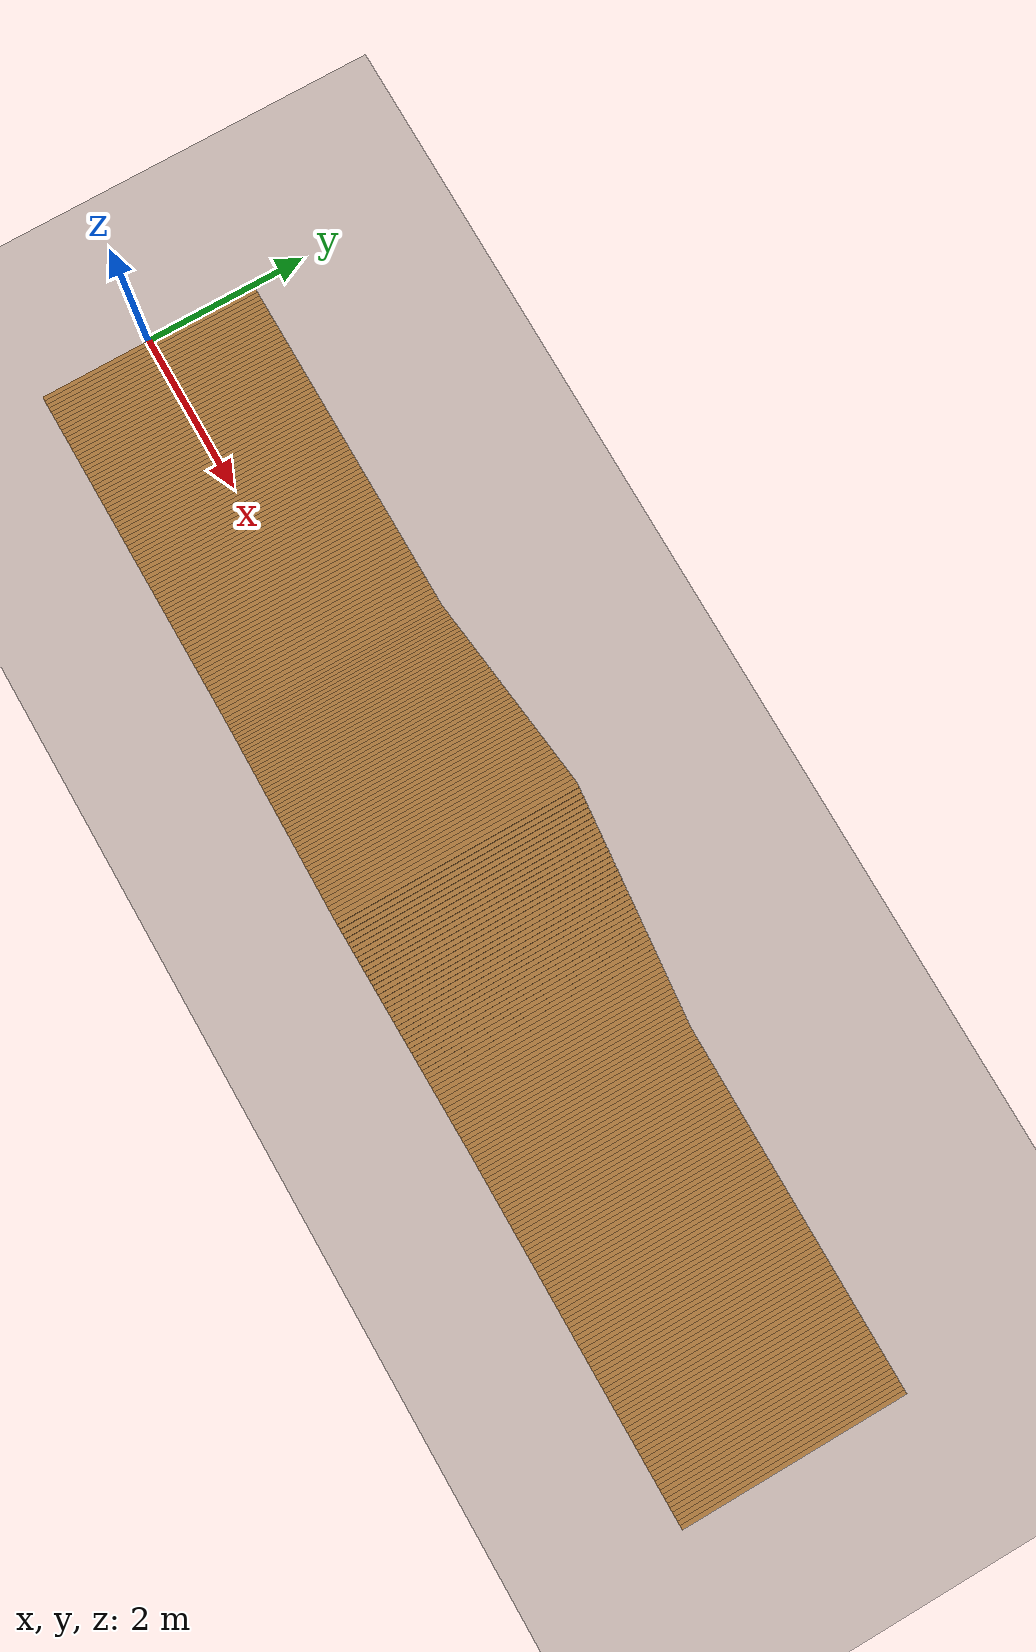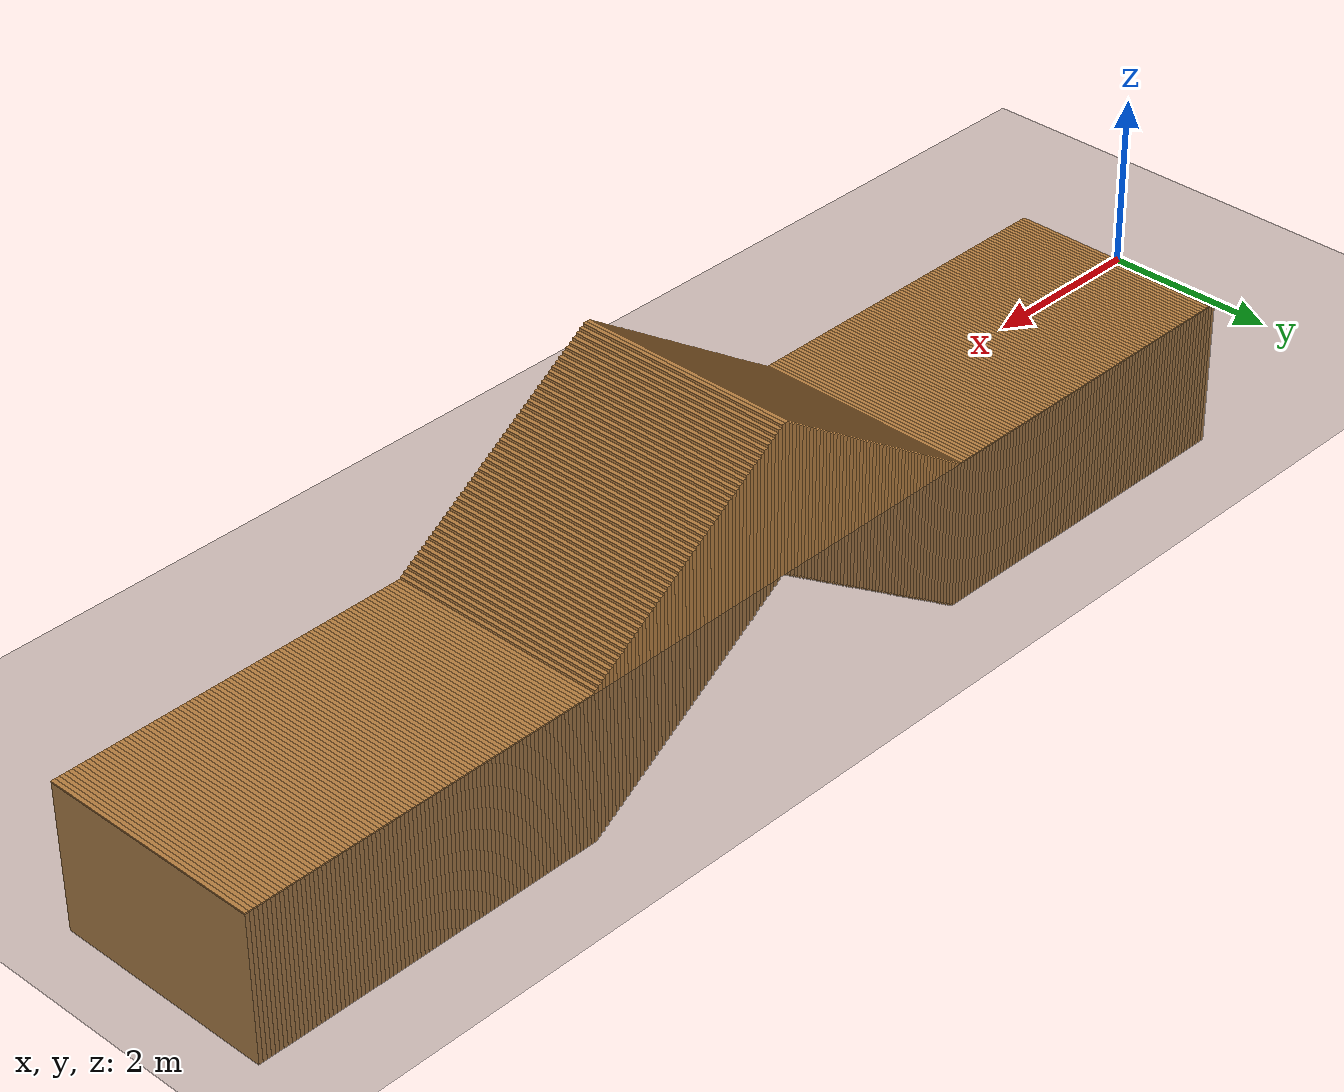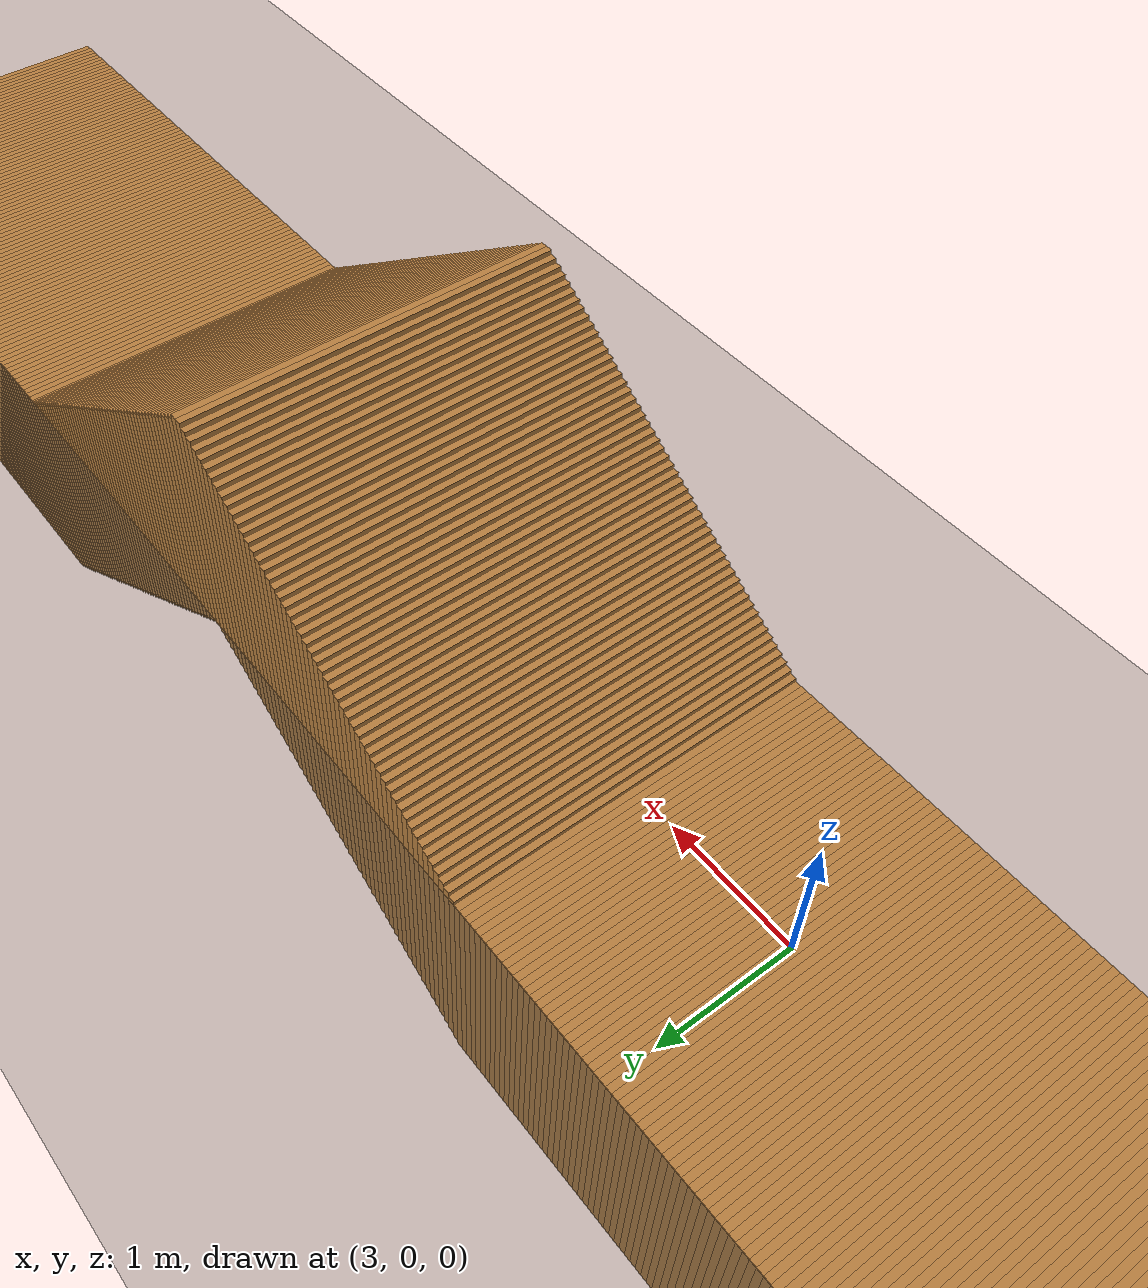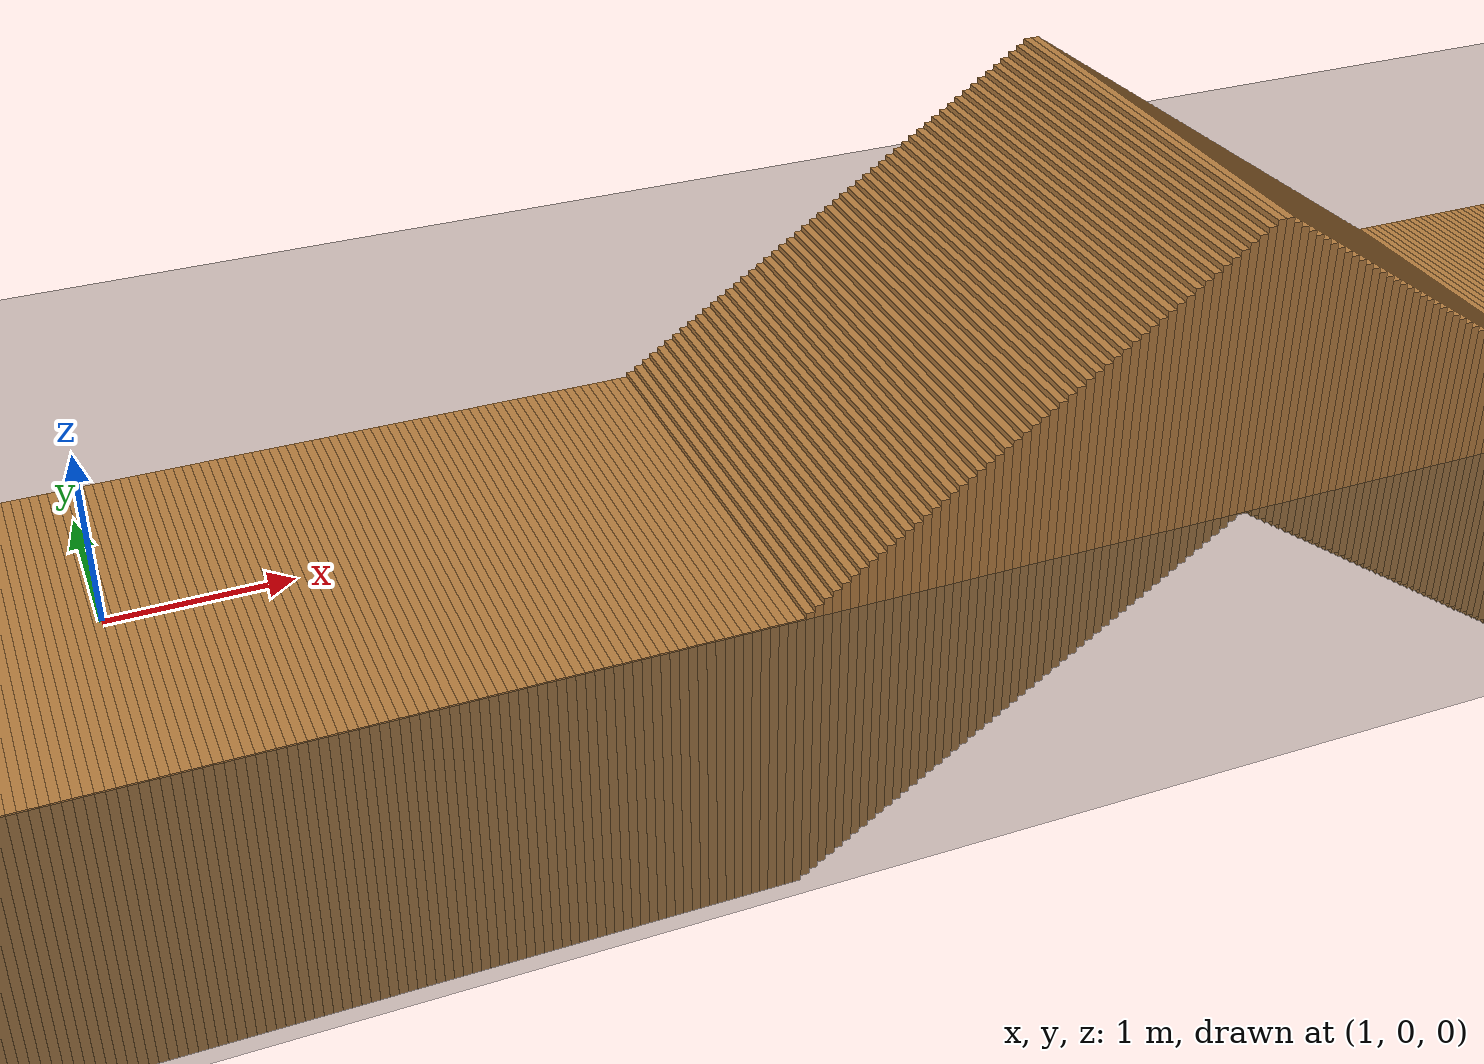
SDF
<?xml version="1.0"?>
<!-- Generated by tools/soil_slice/generate_soil_proxy_world.py. -->
<sdf version="1.10">
  <world name="loader_soil_slice">
    <physics name="loader_500hz" type="dart">
      <max_step_size>0.002</max_step_size>
      <real_time_factor>1.0</real_time_factor>
    </physics>
    <plugin filename="gz-sim-physics-system" name="gz::sim::systems::Physics"/>
    <plugin filename="gz-sim-user-commands-system" name="gz::sim::systems::UserCommands"/>
    <plugin filename="gz-sim-scene-broadcaster-system" name="gz::sim::systems::SceneBroadcaster"/>

    <gravity>0 0 -9.80665</gravity>

    <light name="sun" type="directional">
      <cast_shadows>true</cast_shadows>
      <pose>0 0 10 0 0 0</pose>
      <diffuse>0.8 0.8 0.8 1</diffuse>
      <specular>0.2 0.2 0.2 1</specular>
      <direction>-0.5 0.2 -1</direction>
    </light>

    <model name="rigid_ground">
      <static>true</static>
      <link name="link">
        <collision name="collision">
          <geometry><plane><normal>0 0 1</normal><size>80 40</size></plane></geometry>
          <surface><contact><collide_bitmask>0x01</collide_bitmask></contact></surface>
        </collision>
        <visual name="visual">
          <geometry><plane><normal>0 0 1</normal><size>80 40</size></plane></geometry>
          <material><diffuse>0.30 0.27 0.22 1</diffuse></material>
        </visual>
      </link>
    </model>

    <model name="soil_column_000">
      <static>true</static>
      <pose>0.025000 0 -0.900000 0 0 0</pose>
      <link name="link">
        <visual name="visual">
          <geometry><box><size>0.050000 2.700000 1.800000</size></box></geometry>
          <material>
            <ambient>0.58 0.38 0.18 1</ambient>
            <diffuse>0.72 0.50 0.25 1</diffuse>
          </material>
        </visual>
      </link>
    </model>
    <model name="soil_column_001">
      <static>true</static>
      <pose>0.075000 0 -0.900000 0 0 0</pose>
      <link name="link">
        <visual name="visual">
          <geometry><box><size>0.050000 2.700000 1.800000</size></box></geometry>
          <material>
            <ambient>0.58 0.38 0.18 1</ambient>
            <diffuse>0.72 0.50 0.25 1</diffuse>
          </material>
        </visual>
      </link>
    </model>
    <model name="soil_column_002">
      <static>true</static>
      <pose>0.125000 0 -0.900000 0 0 0</pose>
      <link name="link">
        <visual name="visual">
          <geometry><box><size>0.050000 2.700000 1.800000</size></box></geometry>
          <material>
            <ambient>0.58 0.38 0.18 1</ambient>
            <diffuse>0.72 0.50 0.25 1</diffuse>
          </material>
        </visual>
      </link>
    </model>
    <model name="soil_column_003">
      <static>true</static>
      <pose>0.175000 0 -0.900000 0 0 0</pose>
      <link name="link">
        <visual name="visual">
          <geometry><box><size>0.050000 2.700000 1.800000</size></box></geometry>
          <material>
            <ambient>0.58 0.38 0.18 1</ambient>
            <diffuse>0.72 0.50 0.25 1</diffuse>
          </material>
        </visual>
      </link>
    </model>
    <model name="soil_column_004">
      <static>true</static>
      <pose>0.225000 0 -0.900000 0 0 0</pose>
      <link name="link">
        <visual name="visual">
          <geometry><box><size>0.050000 2.700000 1.800000</size></box></geometry>
          <material>
            <ambient>0.58 0.38 0.18 1</ambient>
            <diffuse>0.72 0.50 0.25 1</diffuse>
          </material>
        </visual>
      </link>
    </model>
    <model name="soil_column_005">
      <static>true</static>
      <pose>0.275000 0 -0.900000 0 0 0</pose>
      <link name="link">
        <visual name="visual">
          <geometry><box><size>0.050000 2.700000 1.800000</size></box></geometry>
          <material>
            <ambient>0.58 0.38 0.18 1</ambient>
            <diffuse>0.72 0.50 0.25 1</diffuse>
          </material>
        </visual>
      </link>
    </model>
    <model name="soil_column_006">
      <static>true</static>
      <pose>0.325000 0 -0.900000 0 0 0</pose>
      <link name="link">
        <visual name="visual">
          <geometry><box><size>0.050000 2.700000 1.800000</size></box></geometry>
          <material>
            <ambient>0.58 0.38 0.18 1</ambient>
            <diffuse>0.72 0.50 0.25 1</diffuse>
          </material>
        </visual>
      </link>
    </model>
    <model name="soil_column_007">
      <static>true</static>
      <pose>0.375000 0 -0.900000 0 0 0</pose>
      <link name="link">
        <visual name="visual">
          <geometry><box><size>0.050000 2.700000 1.800000</size></box></geometry>
          <material>
            <ambient>0.58 0.38 0.18 1</ambient>
            <diffuse>0.72 0.50 0.25 1</diffuse>
          </material>
        </visual>
      </link>
    </model>
    <model name="soil_column_008">
      <static>true</static>
      <pose>0.425000 0 -0.900000 0 0 0</pose>
      <link name="link">
        <visual name="visual">
          <geometry><box><size>0.050000 2.700000 1.800000</size></box></geometry>
          <material>
            <ambient>0.58 0.38 0.18 1</ambient>
            <diffuse>0.72 0.50 0.25 1</diffuse>
          </material>
        </visual>
      </link>
    </model>
    <model name="soil_column_009">
      <static>true</static>
      <pose>0.475000 0 -0.900000 0 0 0</pose>
      <link name="link">
        <visual name="visual">
          <geometry><box><size>0.050000 2.700000 1.800000</size></box></geometry>
          <material>
            <ambient>0.58 0.38 0.18 1</ambient>
            <diffuse>0.72 0.50 0.25 1</diffuse>
          </material>
        </visual>
      </link>
    </model>
    <model name="soil_column_010">
      <static>true</static>
      <pose>0.525000 0 -0.900000 0 0 0</pose>
      <link name="link">
        <visual name="visual">
          <geometry><box><size>0.050000 2.700000 1.800000</size></box></geometry>
          <material>
            <ambient>0.58 0.38 0.18 1</ambient>
            <diffuse>0.72 0.50 0.25 1</diffuse>
          </material>
        </visual>
      </link>
    </model>
    <model name="soil_column_011">
      <static>true</static>
      <pose>0.575000 0 -0.900000 0 0 0</pose>
      <link name="link">
        <visual name="visual">
          <geometry><box><size>0.050000 2.700000 1.800000</size></box></geometry>
          <material>
            <ambient>0.58 0.38 0.18 1</ambient>
            <diffuse>0.72 0.50 0.25 1</diffuse>
          </material>
        </visual>
      </link>
    </model>
    <model name="soil_column_012">
      <static>true</static>
      <pose>0.625000 0 -0.900000 0 0 0</pose>
      <link name="link">
        <visual name="visual">
          <geometry><box><size>0.050000 2.700000 1.800000</size></box></geometry>
          <material>
            <ambient>0.58 0.38 0.18 1</ambient>
            <diffuse>0.72 0.50 0.25 1</diffuse>
          </material>
        </visual>
      </link>
    </model>
    <model name="soil_column_013">
      <static>true</static>
      <pose>0.675000 0 -0.900000 0 0 0</pose>
      <link name="link">
        <visual name="visual">
          <geometry><box><size>0.050000 2.700000 1.800000</size></box></geometry>
          <material>
            <ambient>0.58 0.38 0.18 1</ambient>
            <diffuse>0.72 0.50 0.25 1</diffuse>
          </material>
        </visual>
      </link>
    </model>
    <model name="soil_column_014">
      <static>true</static>
      <pose>0.725000 0 -0.900000 0 0 0</pose>
      <link name="link">
        <visual name="visual">
          <geometry><box><size>0.050000 2.700000 1.800000</size></box></geometry>
          <material>
            <ambient>0.58 0.38 0.18 1</ambient>
            <diffuse>0.72 0.50 0.25 1</diffuse>
          </material>
        </visual>
      </link>
    </model>
    <model name="soil_column_015">
      <static>true</static>
      <pose>0.775000 0 -0.900000 0 0 0</pose>
      <link name="link">
        <visual name="visual">
          <geometry><box><size>0.050000 2.700000 1.800000</size></box></geometry>
          <material>
            <ambient>0.58 0.38 0.18 1</ambient>
            <diffuse>0.72 0.50 0.25 1</diffuse>
          </material>
        </visual>
      </link>
    </model>
    <model name="soil_column_016">
      <static>true</static>
      <pose>0.825000 0 -0.900000 0 0 0</pose>
      <link name="link">
        <visual name="visual">
          <geometry><box><size>0.050000 2.700000 1.800000</size></box></geometry>
          <material>
            <ambient>0.58 0.38 0.18 1</ambient>
            <diffuse>0.72 0.50 0.25 1</diffuse>
          </material>
        </visual>
      </link>
    </model>
    <model name="soil_column_017">
      <static>true</static>
      <pose>0.875000 0 -0.900000 0 0 0</pose>
      <link name="link">
        <visual name="visual">
          <geometry><box><size>0.050000 2.700000 1.800000</size></box></geometry>
          <material>
            <ambient>0.58 0.38 0.18 1</ambient>
            <diffuse>0.72 0.50 0.25 1</diffuse>
          </material>
        </visual>
      </link>
    </model>
    <model name="soil_column_018">
      <static>true</static>
      <pose>0.925000 0 -0.900000 0 0 0</pose>
      <link name="link">
        <visual name="visual">
          <geometry><box><size>0.050000 2.700000 1.800000</size></box></geometry>
          <material>
            <ambient>0.58 0.38 0.18 1</ambient>
            <diffuse>0.72 0.50 0.25 1</diffuse>
          </material>
        </visual>
      </link>
    </model>
    <model name="soil_column_019">
      <static>true</static>
      <pose>0.975000 0 -0.900000 0 0 0</pose>
      <link name="link">
        <visual name="visual">
          <geometry><box><size>0.050000 2.700000 1.800000</size></box></geometry>
          <material>
            <ambient>0.58 0.38 0.18 1</ambient>
            <diffuse>0.72 0.50 0.25 1</diffuse>
          </material>
        </visual>
      </link>
    </model>
    <model name="soil_column_020">
      <static>true</static>
      <pose>1.025000 0 -0.900000 0 0 0</pose>
      <link name="link">
        <visual name="visual">
          <geometry><box><size>0.050000 2.700000 1.800000</size></box></geometry>
          <material>
            <ambient>0.58 0.38 0.18 1</ambient>
            <diffuse>0.72 0.50 0.25 1</diffuse>
          </material>
        </visual>
      </link>
    </model>
    <model name="soil_column_021">
      <static>true</static>
      <pose>1.075000 0 -0.900000 0 0 0</pose>
      <link name="link">
        <visual name="visual">
          <geometry><box><size>0.050000 2.700000 1.800000</size></box></geometry>
          <material>
            <ambient>0.58 0.38 0.18 1</ambient>
            <diffuse>0.72 0.50 0.25 1</diffuse>
          </material>
        </visual>
      </link>
    </model>
    <model name="soil_column_022">
      <static>true</static>
      <pose>1.125000 0 -0.900000 0 0 0</pose>
      <link name="link">
        <visual name="visual">
          <geometry><box><size>0.050000 2.700000 1.800000</size></box></geometry>
          <material>
            <ambient>0.58 0.38 0.18 1</ambient>
            <diffuse>0.72 0.50 0.25 1</diffuse>
          </material>
        </visual>
      </link>
    </model>
    <model name="soil_column_023">
      <static>true</static>
      <pose>1.175000 0 -0.900000 0 0 0</pose>
      <link name="link">
        <visual name="visual">
          <geometry><box><size>0.050000 2.700000 1.800000</size></box></geometry>
          <material>
            <ambient>0.58 0.38 0.18 1</ambient>
            <diffuse>0.72 0.50 0.25 1</diffuse>
          </material>
        </visual>
      </link>
    </model>
    <model name="soil_column_024">
      <static>true</static>
      <pose>1.225000 0 -0.900000 0 0 0</pose>
      <link name="link">
        <visual name="visual">
          <geometry><box><size>0.050000 2.700000 1.800000</size></box></geometry>
          <material>
            <ambient>0.58 0.38 0.18 1</ambient>
            <diffuse>0.72 0.50 0.25 1</diffuse>
          </material>
        </visual>
      </link>
    </model>
    <model name="soil_column_025">
      <static>true</static>
      <pose>1.275000 0 -0.900000 0 0 0</pose>
      <link name="link">
        <visual name="visual">
          <geometry><box><size>0.050000 2.700000 1.800000</size></box></geometry>
          <material>
            <ambient>0.58 0.38 0.18 1</ambient>
            <diffuse>0.72 0.50 0.25 1</diffuse>
          </material>
        </visual>
      </link>
    </model>
    <model name="soil_column_026">
      <static>true</static>
      <pose>1.325000 0 -0.900000 0 0 0</pose>
      <link name="link">
        <visual name="visual">
          <geometry><box><size>0.050000 2.700000 1.800000</size></box></geometry>
          <material>
            <ambient>0.58 0.38 0.18 1</ambient>
            <diffuse>0.72 0.50 0.25 1</diffuse>
          </material>
        </visual>
      </link>
    </model>
    <model name="soil_column_027">
      <static>true</static>
      <pose>1.375000 0 -0.900000 0 0 0</pose>
      <link name="link">
        <visual name="visual">
          <geometry><box><size>0.050000 2.700000 1.800000</size></box></geometry>
          <material>
            <ambient>0.58 0.38 0.18 1</ambient>
            <diffuse>0.72 0.50 0.25 1</diffuse>
          </material>
        </visual>
      </link>
    </model>
    <model name="soil_column_028">
      <static>true</static>
      <pose>1.425000 0 -0.900000 0 0 0</pose>
      <link name="link">
        <visual name="visual">
          <geometry><box><size>0.050000 2.700000 1.800000</size></box></geometry>
          <material>
            <ambient>0.58 0.38 0.18 1</ambient>
            <diffuse>0.72 0.50 0.25 1</diffuse>
          </material>
        </visual>
      </link>
    </model>
    <model name="soil_column_029">
      <static>true</static>
      <pose>1.475000 0 -0.900000 0 0 0</pose>
      <link name="link">
        <visual name="visual">
          <geometry><box><size>0.050000 2.700000 1.800000</size></box></geometry>
          <material>
            <ambient>0.58 0.38 0.18 1</ambient>
            <diffuse>0.72 0.50 0.25 1</diffuse>
          </material>
        </visual>
      </link>
    </model>
    <model name="soil_column_030">
      <static>true</static>
      <pose>1.525000 0 -0.900000 0 0 0</pose>
      <link name="link">
        <visual name="visual">
          <geometry><box><size>0.050000 2.700000 1.800000</size></box></geometry>
          <material>
            <ambient>0.58 0.38 0.18 1</ambient>
            <diffuse>0.72 0.50 0.25 1</diffuse>
          </material>
        </visual>
      </link>
    </model>
    <model name="soil_column_031">
      <static>true</static>
      <pose>1.575000 0 -0.900000 0 0 0</pose>
      <link name="link">
        <visual name="visual">
          <geometry><box><size>0.050000 2.700000 1.800000</size></box></geometry>
          <material>
            <ambient>0.58 0.38 0.18 1</ambient>
            <diffuse>0.72 0.50 0.25 1</diffuse>
          </material>
        </visual>
      </link>
    </model>
    <model name="soil_column_032">
      <static>true</static>
      <pose>1.625000 0 -0.900000 0 0 0</pose>
      <link name="link">
        <visual name="visual">
          <geometry><box><size>0.050000 2.700000 1.800000</size></box></geometry>
          <material>
            <ambient>0.58 0.38 0.18 1</ambient>
            <diffuse>0.72 0.50 0.25 1</diffuse>
          </material>
        </visual>
      </link>
    </model>
    <model name="soil_column_033">
      <static>true</static>
      <pose>1.675000 0 -0.900000 0 0 0</pose>
      <link name="link">
        <visual name="visual">
          <geometry><box><size>0.050000 2.700000 1.800000</size></box></geometry>
          <material>
            <ambient>0.58 0.38 0.18 1</ambient>
            <diffuse>0.72 0.50 0.25 1</diffuse>
          </material>
        </visual>
      </link>
    </model>
    <model name="soil_column_034">
      <static>true</static>
      <pose>1.725000 0 -0.900000 0 0 0</pose>
      <link name="link">
        <visual name="visual">
          <geometry><box><size>0.050000 2.700000 1.800000</size></box></geometry>
          <material>
            <ambient>0.58 0.38 0.18 1</ambient>
            <diffuse>0.72 0.50 0.25 1</diffuse>
          </material>
        </visual>
      </link>
    </model>
    <model name="soil_column_035">
      <static>true</static>
      <pose>1.775000 0 -0.900000 0 0 0</pose>
      <link name="link">
        <visual name="visual">
          <geometry><box><size>0.050000 2.700000 1.800000</size></box></geometry>
          <material>
            <ambient>0.58 0.38 0.18 1</ambient>
            <diffuse>0.72 0.50 0.25 1</diffuse>
          </material>
        </visual>
      </link>
    </model>
    <model name="soil_column_036">
      <static>true</static>
      <pose>1.825000 0 -0.900000 0 0 0</pose>
      <link name="link">
        <visual name="visual">
          <geometry><box><size>0.050000 2.700000 1.800000</size></box></geometry>
          <material>
            <ambient>0.58 0.38 0.18 1</ambient>
            <diffuse>0.72 0.50 0.25 1</diffuse>
          </material>
        </visual>
      </link>
    </model>
    <model name="soil_column_037">
      <static>true</static>
      <pose>1.875000 0 -0.900000 0 0 0</pose>
      <link name="link">
        <visual name="visual">
          <geometry><box><size>0.050000 2.700000 1.800000</size></box></geometry>
          <material>
            <ambient>0.58 0.38 0.18 1</ambient>
            <diffuse>0.72 0.50 0.25 1</diffuse>
          </material>
        </visual>
      </link>
    </model>
    <model name="soil_column_038">
      <static>true</static>
      <pose>1.925000 0 -0.900000 0 0 0</pose>
      <link name="link">
        <visual name="visual">
          <geometry><box><size>0.050000 2.700000 1.800000</size></box></geometry>
          <material>
            <ambient>0.58 0.38 0.18 1</ambient>
            <diffuse>0.72 0.50 0.25 1</diffuse>
          </material>
        </visual>
      </link>
    </model>
    <model name="soil_column_039">
      <static>true</static>
      <pose>1.975000 0 -0.900000 0 0 0</pose>
      <link name="link">
        <visual name="visual">
          <geometry><box><size>0.050000 2.700000 1.800000</size></box></geometry>
          <material>
            <ambient>0.58 0.38 0.18 1</ambient>
            <diffuse>0.72 0.50 0.25 1</diffuse>
          </material>
        </visual>
      </link>
    </model>
    <model name="soil_column_040">
      <static>true</static>
      <pose>2.025000 0 -0.900000 0 0 0</pose>
      <link name="link">
        <visual name="visual">
          <geometry><box><size>0.050000 2.700000 1.800000</size></box></geometry>
          <material>
            <ambient>0.58 0.38 0.18 1</ambient>
            <diffuse>0.72 0.50 0.25 1</diffuse>
          </material>
        </visual>
      </link>
    </model>
    <model name="soil_column_041">
      <static>true</static>
      <pose>2.075000 0 -0.900000 0 0 0</pose>
      <link name="link">
        <visual name="visual">
          <geometry><box><size>0.050000 2.700000 1.800000</size></box></geometry>
          <material>
            <ambient>0.58 0.38 0.18 1</ambient>
            <diffuse>0.72 0.50 0.25 1</diffuse>
          </material>
        </visual>
      </link>
    </model>
    <model name="soil_column_042">
      <static>true</static>
      <pose>2.125000 0 -0.900000 0 0 0</pose>
      <link name="link">
        <visual name="visual">
          <geometry><box><size>0.050000 2.700000 1.800000</size></box></geometry>
          <material>
            <ambient>0.58 0.38 0.18 1</ambient>
            <diffuse>0.72 0.50 0.25 1</diffuse>
          </material>
        </visual>
      </link>
    </model>
    <model name="soil_column_043">
      <static>true</static>
      <pose>2.175000 0 -0.900000 0 0 0</pose>
      <link name="link">
        <visual name="visual">
          <geometry><box><size>0.050000 2.700000 1.800000</size></box></geometry>
          <material>
            <ambient>0.58 0.38 0.18 1</ambient>
            <diffuse>0.72 0.50 0.25 1</diffuse>
          </material>
        </visual>
      </link>
    </model>
    <model name="soil_column_044">
      <static>true</static>
      <pose>2.225000 0 -0.900000 0 0 0</pose>
      <link name="link">
        <visual name="visual">
          <geometry><box><size>0.050000 2.700000 1.800000</size></box></geometry>
          <material>
            <ambient>0.58 0.38 0.18 1</ambient>
            <diffuse>0.72 0.50 0.25 1</diffuse>
          </material>
        </visual>
      </link>
    </model>
    <model name="soil_column_045">
      <static>true</static>
      <pose>2.275000 0 -0.900000 0 0 0</pose>
      <link name="link">
        <visual name="visual">
          <geometry><box><size>0.050000 2.700000 1.800000</size></box></geometry>
          <material>
            <ambient>0.58 0.38 0.18 1</ambient>
            <diffuse>0.72 0.50 0.25 1</diffuse>
          </material>
        </visual>
      </link>
    </model>
    <model name="soil_column_046">
      <static>true</static>
      <pose>2.325000 0 -0.900000 0 0 0</pose>
      <link name="link">
        <visual name="visual">
          <geometry><box><size>0.050000 2.700000 1.800000</size></box></geometry>
          <material>
            <ambient>0.58 0.38 0.18 1</ambient>
            <diffuse>0.72 0.50 0.25 1</diffuse>
          </material>
        </visual>
      </link>
    </model>
    <model name="soil_column_047">
      <static>true</static>
      <pose>2.375000 0 -0.900000 0 0 0</pose>
      <link name="link">
        <visual name="visual">
          <geometry><box><size>0.050000 2.700000 1.800000</size></box></geometry>
          <material>
            <ambient>0.58 0.38 0.18 1</ambient>
            <diffuse>0.72 0.50 0.25 1</diffuse>
          </material>
        </visual>
      </link>
    </model>
    <model name="soil_column_048">
      <static>true</static>
      <pose>2.425000 0 -0.900000 0 0 0</pose>
      <link name="link">
        <visual name="visual">
          <geometry><box><size>0.050000 2.700000 1.800000</size></box></geometry>
          <material>
            <ambient>0.58 0.38 0.18 1</ambient>
            <diffuse>0.72 0.50 0.25 1</diffuse>
          </material>
        </visual>
      </link>
    </model>
    <model name="soil_column_049">
      <static>true</static>
      <pose>2.475000 0 -0.900000 0 0 0</pose>
      <link name="link">
        <visual name="visual">
          <geometry><box><size>0.050000 2.700000 1.800000</size></box></geometry>
          <material>
            <ambient>0.58 0.38 0.18 1</ambient>
            <diffuse>0.72 0.50 0.25 1</diffuse>
          </material>
        </visual>
      </link>
    </model>
    <model name="soil_column_050">
      <static>true</static>
      <pose>2.525000 0 -0.900000 0 0 0</pose>
      <link name="link">
        <visual name="visual">
          <geometry><box><size>0.050000 2.700000 1.800000</size></box></geometry>
          <material>
            <ambient>0.58 0.38 0.18 1</ambient>
            <diffuse>0.72 0.50 0.25 1</diffuse>
          </material>
        </visual>
      </link>
    </model>
    <model name="soil_column_051">
      <static>true</static>
      <pose>2.575000 0 -0.900000 0 0 0</pose>
      <link name="link">
        <visual name="visual">
          <geometry><box><size>0.050000 2.700000 1.800000</size></box></geometry>
          <material>
            <ambient>0.58 0.38 0.18 1</ambient>
            <diffuse>0.72 0.50 0.25 1</diffuse>
          </material>
        </visual>
      </link>
    </model>
    <model name="soil_column_052">
      <static>true</static>
      <pose>2.625000 0 -0.900000 0 0 0</pose>
      <link name="link">
        <visual name="visual">
          <geometry><box><size>0.050000 2.700000 1.800000</size></box></geometry>
          <material>
            <ambient>0.58 0.38 0.18 1</ambient>
            <diffuse>0.72 0.50 0.25 1</diffuse>
          </material>
        </visual>
      </link>
    </model>
    <model name="soil_column_053">
      <static>true</static>
      <pose>2.675000 0 -0.900000 0 0 0</pose>
      <link name="link">
        <visual name="visual">
          <geometry><box><size>0.050000 2.700000 1.800000</size></box></geometry>
          <material>
            <ambient>0.58 0.38 0.18 1</ambient>
            <diffuse>0.72 0.50 0.25 1</diffuse>
          </material>
        </visual>
      </link>
    </model>
    <model name="soil_column_054">
      <static>true</static>
      <pose>2.725000 0 -0.900000 0 0 0</pose>
      <link name="link">
        <visual name="visual">
          <geometry><box><size>0.050000 2.700000 1.800000</size></box></geometry>
          <material>
            <ambient>0.58 0.38 0.18 1</ambient>
            <diffuse>0.72 0.50 0.25 1</diffuse>
          </material>
        </visual>
      </link>
    </model>
    <model name="soil_column_055">
      <static>true</static>
      <pose>2.775000 0 -0.900000 0 0 0</pose>
      <link name="link">
        <visual name="visual">
          <geometry><box><size>0.050000 2.700000 1.800000</size></box></geometry>
          <material>
            <ambient>0.58 0.38 0.18 1</ambient>
            <diffuse>0.72 0.50 0.25 1</diffuse>
          </material>
        </visual>
      </link>
    </model>
    <model name="soil_column_056">
      <static>true</static>
      <pose>2.825000 0 -0.900000 0 0 0</pose>
      <link name="link">
        <visual name="visual">
          <geometry><box><size>0.050000 2.700000 1.800000</size></box></geometry>
          <material>
            <ambient>0.58 0.38 0.18 1</ambient>
            <diffuse>0.72 0.50 0.25 1</diffuse>
          </material>
        </visual>
      </link>
    </model>
    <model name="soil_column_057">
      <static>true</static>
      <pose>2.875000 0 -0.900000 0 0 0</pose>
      <link name="link">
        <visual name="visual">
          <geometry><box><size>0.050000 2.700000 1.800000</size></box></geometry>
          <material>
            <ambient>0.58 0.38 0.18 1</ambient>
            <diffuse>0.72 0.50 0.25 1</diffuse>
          </material>
        </visual>
      </link>
    </model>
    <model name="soil_column_058">
      <static>true</static>
      <pose>2.925000 0 -0.900000 0 0 0</pose>
      <link name="link">
        <visual name="visual">
          <geometry><box><size>0.050000 2.700000 1.800000</size></box></geometry>
          <material>
            <ambient>0.58 0.38 0.18 1</ambient>
            <diffuse>0.72 0.50 0.25 1</diffuse>
          </material>
        </visual>
      </link>
    </model>
    <model name="soil_column_059">
      <static>true</static>
      <pose>2.975000 0 -0.900000 0 0 0</pose>
      <link name="link">
        <visual name="visual">
          <geometry><box><size>0.050000 2.700000 1.800000</size></box></geometry>
          <material>
            <ambient>0.58 0.38 0.18 1</ambient>
            <diffuse>0.72 0.50 0.25 1</diffuse>
          </material>
        </visual>
      </link>
    </model>
    <model name="soil_column_060">
      <static>true</static>
      <pose>3.025000 0 -0.900000 0 0 0</pose>
      <link name="link">
        <visual name="visual">
          <geometry><box><size>0.050000 2.700000 1.800000</size></box></geometry>
          <material>
            <ambient>0.58 0.38 0.18 1</ambient>
            <diffuse>0.72 0.50 0.25 1</diffuse>
          </material>
        </visual>
      </link>
    </model>
    <model name="soil_column_061">
      <static>true</static>
      <pose>3.075000 0 -0.900000 0 0 0</pose>
      <link name="link">
        <visual name="visual">
          <geometry><box><size>0.050000 2.700000 1.800000</size></box></geometry>
          <material>
            <ambient>0.58 0.38 0.18 1</ambient>
            <diffuse>0.72 0.50 0.25 1</diffuse>
          </material>
        </visual>
      </link>
    </model>
    <model name="soil_column_062">
      <static>true</static>
      <pose>3.125000 0 -0.900000 0 0 0</pose>
      <link name="link">
        <visual name="visual">
          <geometry><box><size>0.050000 2.700000 1.800000</size></box></geometry>
          <material>
            <ambient>0.58 0.38 0.18 1</ambient>
            <diffuse>0.72 0.50 0.25 1</diffuse>
          </material>
        </visual>
      </link>
    </model>
    <model name="soil_column_063">
      <static>true</static>
      <pose>3.175000 0 -0.900000 0 0 0</pose>
      <link name="link">
        <visual name="visual">
          <geometry><box><size>0.050000 2.700000 1.800000</size></box></geometry>
          <material>
            <ambient>0.58 0.38 0.18 1</ambient>
            <diffuse>0.72 0.50 0.25 1</diffuse>
          </material>
        </visual>
      </link>
    </model>
    <model name="soil_column_064">
      <static>true</static>
      <pose>3.225000 0 -0.900000 0 0 0</pose>
      <link name="link">
        <visual name="visual">
          <geometry><box><size>0.050000 2.700000 1.800000</size></box></geometry>
          <material>
            <ambient>0.58 0.38 0.18 1</ambient>
            <diffuse>0.72 0.50 0.25 1</diffuse>
          </material>
        </visual>
      </link>
    </model>
    <model name="soil_column_065">
      <static>true</static>
      <pose>3.275000 0 -0.900000 0 0 0</pose>
      <link name="link">
        <visual name="visual">
          <geometry><box><size>0.050000 2.700000 1.800000</size></box></geometry>
          <material>
            <ambient>0.58 0.38 0.18 1</ambient>
            <diffuse>0.72 0.50 0.25 1</diffuse>
          </material>
        </visual>
      </link>
    </model>
    <model name="soil_column_066">
      <static>true</static>
      <pose>3.325000 0 -0.900000 0 0 0</pose>
      <link name="link">
        <visual name="visual">
          <geometry><box><size>0.050000 2.700000 1.800000</size></box></geometry>
          <material>
            <ambient>0.58 0.38 0.18 1</ambient>
            <diffuse>0.72 0.50 0.25 1</diffuse>
          </material>
        </visual>
      </link>
    </model>
    <model name="soil_column_067">
      <static>true</static>
      <pose>3.375000 0 -0.900000 0 0 0</pose>
      <link name="link">
        <visual name="visual">
          <geometry><box><size>0.050000 2.700000 1.800000</size></box></geometry>
          <material>
            <ambient>0.58 0.38 0.18 1</ambient>
            <diffuse>0.72 0.50 0.25 1</diffuse>
          </material>
        </visual>
      </link>
    </model>
    <model name="soil_column_068">
      <static>true</static>
      <pose>3.425000 0 -0.900000 0 0 0</pose>
      <link name="link">
        <visual name="visual">
          <geometry><box><size>0.050000 2.700000 1.800000</size></box></geometry>
          <material>
            <ambient>0.58 0.38 0.18 1</ambient>
            <diffuse>0.72 0.50 0.25 1</diffuse>
          </material>
        </visual>
      </link>
    </model>
    <model name="soil_column_069">
      <static>true</static>
      <pose>3.475000 0 -0.900000 0 0 0</pose>
      <link name="link">
        <visual name="visual">
          <geometry><box><size>0.050000 2.700000 1.800000</size></box></geometry>
          <material>
            <ambient>0.58 0.38 0.18 1</ambient>
            <diffuse>0.72 0.50 0.25 1</diffuse>
          </material>
        </visual>
      </link>
    </model>
    <model name="soil_column_070">
      <static>true</static>
      <pose>3.525000 0 -0.900000 0 0 0</pose>
      <link name="link">
        <visual name="visual">
          <geometry><box><size>0.050000 2.700000 1.800000</size></box></geometry>
          <material>
            <ambient>0.58 0.38 0.18 1</ambient>
            <diffuse>0.72 0.50 0.25 1</diffuse>
          </material>
        </visual>
      </link>
    </model>
    <model name="soil_column_071">
      <static>true</static>
      <pose>3.575000 0 -0.900000 0 0 0</pose>
      <link name="link">
        <visual name="visual">
          <geometry><box><size>0.050000 2.700000 1.800000</size></box></geometry>
          <material>
            <ambient>0.58 0.38 0.18 1</ambient>
            <diffuse>0.72 0.50 0.25 1</diffuse>
          </material>
        </visual>
      </link>
    </model>
    <model name="soil_column_072">
      <static>true</static>
      <pose>3.625000 0 -0.900000 0 0 0</pose>
      <link name="link">
        <visual name="visual">
          <geometry><box><size>0.050000 2.700000 1.800000</size></box></geometry>
          <material>
            <ambient>0.58 0.38 0.18 1</ambient>
            <diffuse>0.72 0.50 0.25 1</diffuse>
          </material>
        </visual>
      </link>
    </model>
    <model name="soil_column_073">
      <static>true</static>
      <pose>3.675000 0 -0.900000 0 0 0</pose>
      <link name="link">
        <visual name="visual">
          <geometry><box><size>0.050000 2.700000 1.800000</size></box></geometry>
          <material>
            <ambient>0.58 0.38 0.18 1</ambient>
            <diffuse>0.72 0.50 0.25 1</diffuse>
          </material>
        </visual>
      </link>
    </model>
    <model name="soil_column_074">
      <static>true</static>
      <pose>3.725000 0 -0.900000 0 0 0</pose>
      <link name="link">
        <visual name="visual">
          <geometry><box><size>0.050000 2.700000 1.800000</size></box></geometry>
          <material>
            <ambient>0.58 0.38 0.18 1</ambient>
            <diffuse>0.72 0.50 0.25 1</diffuse>
          </material>
        </visual>
      </link>
    </model>
    <model name="soil_column_075">
      <static>true</static>
      <pose>3.775000 0 -0.900000 0 0 0</pose>
      <link name="link">
        <visual name="visual">
          <geometry><box><size>0.050000 2.700000 1.800000</size></box></geometry>
          <material>
            <ambient>0.58 0.38 0.18 1</ambient>
            <diffuse>0.72 0.50 0.25 1</diffuse>
          </material>
        </visual>
      </link>
    </model>
    <model name="soil_column_076">
      <static>true</static>
      <pose>3.825000 0 -0.900000 0 0 0</pose>
      <link name="link">
        <visual name="visual">
          <geometry><box><size>0.050000 2.700000 1.800000</size></box></geometry>
          <material>
            <ambient>0.58 0.38 0.18 1</ambient>
            <diffuse>0.72 0.50 0.25 1</diffuse>
          </material>
        </visual>
      </link>
    </model>
    <model name="soil_column_077">
      <static>true</static>
      <pose>3.875000 0 -0.900000 0 0 0</pose>
      <link name="link">
        <visual name="visual">
          <geometry><box><size>0.050000 2.700000 1.800000</size></box></geometry>
          <material>
            <ambient>0.58 0.38 0.18 1</ambient>
            <diffuse>0.72 0.50 0.25 1</diffuse>
          </material>
        </visual>
      </link>
    </model>
    <model name="soil_column_078">
      <static>true</static>
      <pose>3.925000 0 -0.900000 0 0 0</pose>
      <link name="link">
        <visual name="visual">
          <geometry><box><size>0.050000 2.700000 1.800000</size></box></geometry>
          <material>
            <ambient>0.58 0.38 0.18 1</ambient>
            <diffuse>0.72 0.50 0.25 1</diffuse>
          </material>
        </visual>
      </link>
    </model>
    <model name="soil_column_079">
      <static>true</static>
      <pose>3.975000 0 -0.900000 0 0 0</pose>
      <link name="link">
        <visual name="visual">
          <geometry><box><size>0.050000 2.700000 1.800000</size></box></geometry>
          <material>
            <ambient>0.58 0.38 0.18 1</ambient>
            <diffuse>0.72 0.50 0.25 1</diffuse>
          </material>
        </visual>
      </link>
    </model>
    <model name="soil_column_080">
      <static>true</static>
      <pose>4.025000 0 -0.900000 0 0 0</pose>
      <link name="link">
        <visual name="visual">
          <geometry><box><size>0.050000 2.700000 1.800000</size></box></geometry>
          <material>
            <ambient>0.58 0.38 0.18 1</ambient>
            <diffuse>0.72 0.50 0.25 1</diffuse>
          </material>
        </visual>
      </link>
    </model>
    <model name="soil_column_081">
      <static>true</static>
      <pose>4.075000 0 -0.900000 0 0 0</pose>
      <link name="link">
        <visual name="visual">
          <geometry><box><size>0.050000 2.700000 1.800000</size></box></geometry>
          <material>
            <ambient>0.58 0.38 0.18 1</ambient>
            <diffuse>0.72 0.50 0.25 1</diffuse>
          </material>
        </visual>
      </link>
    </model>
    <model name="soil_column_082">
      <static>true</static>
      <pose>4.125000 0 -0.900000 0 0 0</pose>
      <link name="link">
        <visual name="visual">
          <geometry><box><size>0.050000 2.700000 1.800000</size></box></geometry>
          <material>
            <ambient>0.58 0.38 0.18 1</ambient>
            <diffuse>0.72 0.50 0.25 1</diffuse>
          </material>
        </visual>
      </link>
    </model>
    <model name="soil_column_083">
      <static>true</static>
      <pose>4.175000 0 -0.900000 0 0 0</pose>
      <link name="link">
        <visual name="visual">
          <geometry><box><size>0.050000 2.700000 1.800000</size></box></geometry>
          <material>
            <ambient>0.58 0.38 0.18 1</ambient>
            <diffuse>0.72 0.50 0.25 1</diffuse>
          </material>
        </visual>
      </link>
    </model>
    <model name="soil_column_084">
      <static>true</static>
      <pose>4.225000 0 -0.900000 0 0 0</pose>
      <link name="link">
        <visual name="visual">
          <geometry><box><size>0.050000 2.700000 1.800000</size></box></geometry>
          <material>
            <ambient>0.58 0.38 0.18 1</ambient>
            <diffuse>0.72 0.50 0.25 1</diffuse>
          </material>
        </visual>
      </link>
    </model>
    <model name="soil_column_085">
      <static>true</static>
      <pose>4.275000 0 -0.900000 0 0 0</pose>
      <link name="link">
        <visual name="visual">
          <geometry><box><size>0.050000 2.700000 1.800000</size></box></geometry>
          <material>
            <ambient>0.58 0.38 0.18 1</ambient>
            <diffuse>0.72 0.50 0.25 1</diffuse>
          </material>
        </visual>
      </link>
    </model>
    <model name="soil_column_086">
      <static>true</static>
      <pose>4.325000 0 -0.900000 0 0 0</pose>
      <link name="link">
        <visual name="visual">
          <geometry><box><size>0.050000 2.700000 1.800000</size></box></geometry>
          <material>
            <ambient>0.58 0.38 0.18 1</ambient>
            <diffuse>0.72 0.50 0.25 1</diffuse>
          </material>
        </visual>
      </link>
    </model>
    <model name="soil_column_087">
      <static>true</static>
      <pose>4.375000 0 -0.870585 0 0 0</pose>
      <link name="link">
        <visual name="visual">
          <geometry><box><size>0.050000 2.700000 1.800000</size></box></geometry>
          <material>
            <ambient>0.58 0.38 0.18 1</ambient>
            <diffuse>0.72 0.50 0.25 1</diffuse>
          </material>
        </visual>
      </link>
    </model>
    <model name="soil_column_088">
      <static>true</static>
      <pose>4.425000 0 -0.836859 0 0 0</pose>
      <link name="link">
        <visual name="visual">
          <geometry><box><size>0.050000 2.700000 1.800000</size></box></geometry>
          <material>
            <ambient>0.58 0.38 0.18 1</ambient>
            <diffuse>0.72 0.50 0.25 1</diffuse>
          </material>
        </visual>
      </link>
    </model>
    <model name="soil_column_089">
      <static>true</static>
      <pose>4.475000 0 -0.803134 0 0 0</pose>
      <link name="link">
        <visual name="visual">
          <geometry><box><size>0.050000 2.700000 1.800000</size></box></geometry>
          <material>
            <ambient>0.58 0.38 0.18 1</ambient>
            <diffuse>0.72 0.50 0.25 1</diffuse>
          </material>
        </visual>
      </link>
    </model>
    <model name="soil_column_090">
      <static>true</static>
      <pose>4.525000 0 -0.769409 0 0 0</pose>
      <link name="link">
        <visual name="visual">
          <geometry><box><size>0.050000 2.700000 1.800000</size></box></geometry>
          <material>
            <ambient>0.58 0.38 0.18 1</ambient>
            <diffuse>0.72 0.50 0.25 1</diffuse>
          </material>
        </visual>
      </link>
    </model>
    <model name="soil_column_091">
      <static>true</static>
      <pose>4.575000 0 -0.735683 0 0 0</pose>
      <link name="link">
        <visual name="visual">
          <geometry><box><size>0.050000 2.700000 1.800000</size></box></geometry>
          <material>
            <ambient>0.58 0.38 0.18 1</ambient>
            <diffuse>0.72 0.50 0.25 1</diffuse>
          </material>
        </visual>
      </link>
    </model>
    <model name="soil_column_092">
      <static>true</static>
      <pose>4.625000 0 -0.701958 0 0 0</pose>
      <link name="link">
        <visual name="visual">
          <geometry><box><size>0.050000 2.700000 1.800000</size></box></geometry>
          <material>
            <ambient>0.58 0.38 0.18 1</ambient>
            <diffuse>0.72 0.50 0.25 1</diffuse>
          </material>
        </visual>
      </link>
    </model>
    <model name="soil_column_093">
      <static>true</static>
      <pose>4.675000 0 -0.668232 0 0 0</pose>
      <link name="link">
        <visual name="visual">
          <geometry><box><size>0.050000 2.700000 1.800000</size></box></geometry>
          <material>
            <ambient>0.58 0.38 0.18 1</ambient>
            <diffuse>0.72 0.50 0.25 1</diffuse>
          </material>
        </visual>
      </link>
    </model>
    <model name="soil_column_094">
      <static>true</static>
      <pose>4.725000 0 -0.634507 0 0 0</pose>
      <link name="link">
        <visual name="visual">
          <geometry><box><size>0.050000 2.700000 1.800000</size></box></geometry>
          <material>
            <ambient>0.58 0.38 0.18 1</ambient>
            <diffuse>0.72 0.50 0.25 1</diffuse>
          </material>
        </visual>
      </link>
    </model>
    <model name="soil_column_095">
      <static>true</static>
      <pose>4.775000 0 -0.600781 0 0 0</pose>
      <link name="link">
        <visual name="visual">
          <geometry><box><size>0.050000 2.700000 1.800000</size></box></geometry>
          <material>
            <ambient>0.58 0.38 0.18 1</ambient>
            <diffuse>0.72 0.50 0.25 1</diffuse>
          </material>
        </visual>
      </link>
    </model>
    <model name="soil_column_096">
      <static>true</static>
      <pose>4.825000 0 -0.567056 0 0 0</pose>
      <link name="link">
        <visual name="visual">
          <geometry><box><size>0.050000 2.700000 1.800000</size></box></geometry>
          <material>
            <ambient>0.58 0.38 0.18 1</ambient>
            <diffuse>0.72 0.50 0.25 1</diffuse>
          </material>
        </visual>
      </link>
    </model>
    <model name="soil_column_097">
      <static>true</static>
      <pose>4.875000 0 -0.533331 0 0 0</pose>
      <link name="link">
        <visual name="visual">
          <geometry><box><size>0.050000 2.700000 1.800000</size></box></geometry>
          <material>
            <ambient>0.58 0.38 0.18 1</ambient>
            <diffuse>0.72 0.50 0.25 1</diffuse>
          </material>
        </visual>
      </link>
    </model>
    <model name="soil_column_098">
      <static>true</static>
      <pose>4.925000 0 -0.499605 0 0 0</pose>
      <link name="link">
        <visual name="visual">
          <geometry><box><size>0.050000 2.700000 1.800000</size></box></geometry>
          <material>
            <ambient>0.58 0.38 0.18 1</ambient>
            <diffuse>0.72 0.50 0.25 1</diffuse>
          </material>
        </visual>
      </link>
    </model>
    <model name="soil_column_099">
      <static>true</static>
      <pose>4.975000 0 -0.465880 0 0 0</pose>
      <link name="link">
        <visual name="visual">
          <geometry><box><size>0.050000 2.700000 1.800000</size></box></geometry>
          <material>
            <ambient>0.58 0.38 0.18 1</ambient>
            <diffuse>0.72 0.50 0.25 1</diffuse>
          </material>
        </visual>
      </link>
    </model>
    <model name="soil_column_100">
      <static>true</static>
      <pose>5.025000 0 -0.432154 0 0 0</pose>
      <link name="link">
        <visual name="visual">
          <geometry><box><size>0.050000 2.700000 1.800000</size></box></geometry>
          <material>
            <ambient>0.58 0.38 0.18 1</ambient>
            <diffuse>0.72 0.50 0.25 1</diffuse>
          </material>
        </visual>
      </link>
    </model>
    <model name="soil_column_101">
      <static>true</static>
      <pose>5.075000 0 -0.398429 0 0 0</pose>
      <link name="link">
        <visual name="visual">
          <geometry><box><size>0.050000 2.700000 1.800000</size></box></geometry>
          <material>
            <ambient>0.58 0.38 0.18 1</ambient>
            <diffuse>0.72 0.50 0.25 1</diffuse>
          </material>
        </visual>
      </link>
    </model>
    <model name="soil_column_102">
      <static>true</static>
      <pose>5.125000 0 -0.364703 0 0 0</pose>
      <link name="link">
        <visual name="visual">
          <geometry><box><size>0.050000 2.700000 1.800000</size></box></geometry>
          <material>
            <ambient>0.58 0.38 0.18 1</ambient>
            <diffuse>0.72 0.50 0.25 1</diffuse>
          </material>
        </visual>
      </link>
    </model>
    <model name="soil_column_103">
      <static>true</static>
      <pose>5.175000 0 -0.330978 0 0 0</pose>
      <link name="link">
        <visual name="visual">
          <geometry><box><size>0.050000 2.700000 1.800000</size></box></geometry>
          <material>
            <ambient>0.58 0.38 0.18 1</ambient>
            <diffuse>0.72 0.50 0.25 1</diffuse>
          </material>
        </visual>
      </link>
    </model>
    <model name="soil_column_104">
      <static>true</static>
      <pose>5.225000 0 -0.297253 0 0 0</pose>
      <link name="link">
        <visual name="visual">
          <geometry><box><size>0.050000 2.700000 1.800000</size></box></geometry>
          <material>
            <ambient>0.58 0.38 0.18 1</ambient>
            <diffuse>0.72 0.50 0.25 1</diffuse>
          </material>
        </visual>
      </link>
    </model>
    <model name="soil_column_105">
      <static>true</static>
      <pose>5.275000 0 -0.263527 0 0 0</pose>
      <link name="link">
        <visual name="visual">
          <geometry><box><size>0.050000 2.700000 1.800000</size></box></geometry>
          <material>
            <ambient>0.58 0.38 0.18 1</ambient>
            <diffuse>0.72 0.50 0.25 1</diffuse>
          </material>
        </visual>
      </link>
    </model>
    <model name="soil_column_106">
      <static>true</static>
      <pose>5.325000 0 -0.229802 0 0 0</pose>
      <link name="link">
        <visual name="visual">
          <geometry><box><size>0.050000 2.700000 1.800000</size></box></geometry>
          <material>
            <ambient>0.58 0.38 0.18 1</ambient>
            <diffuse>0.72 0.50 0.25 1</diffuse>
          </material>
        </visual>
      </link>
    </model>
    <model name="soil_column_107">
      <static>true</static>
      <pose>5.375000 0 -0.196076 0 0 0</pose>
      <link name="link">
        <visual name="visual">
          <geometry><box><size>0.050000 2.700000 1.800000</size></box></geometry>
          <material>
            <ambient>0.58 0.38 0.18 1</ambient>
            <diffuse>0.72 0.50 0.25 1</diffuse>
          </material>
        </visual>
      </link>
    </model>
    <model name="soil_column_108">
      <static>true</static>
      <pose>5.425000 0 -0.162351 0 0 0</pose>
      <link name="link">
        <visual name="visual">
          <geometry><box><size>0.050000 2.700000 1.800000</size></box></geometry>
          <material>
            <ambient>0.58 0.38 0.18 1</ambient>
            <diffuse>0.72 0.50 0.25 1</diffuse>
          </material>
        </visual>
      </link>
    </model>
    <model name="soil_column_109">
      <static>true</static>
      <pose>5.475000 0 -0.128625 0 0 0</pose>
      <link name="link">
        <visual name="visual">
          <geometry><box><size>0.050000 2.700000 1.800000</size></box></geometry>
          <material>
            <ambient>0.58 0.38 0.18 1</ambient>
            <diffuse>0.72 0.50 0.25 1</diffuse>
          </material>
        </visual>
      </link>
    </model>
    <model name="soil_column_110">
      <static>true</static>
      <pose>5.525000 0 -0.094900 0 0 0</pose>
      <link name="link">
        <visual name="visual">
          <geometry><box><size>0.050000 2.700000 1.800000</size></box></geometry>
          <material>
            <ambient>0.58 0.38 0.18 1</ambient>
            <diffuse>0.72 0.50 0.25 1</diffuse>
          </material>
        </visual>
      </link>
    </model>
    <model name="soil_column_111">
      <static>true</static>
      <pose>5.575000 0 -0.061175 0 0 0</pose>
      <link name="link">
        <visual name="visual">
          <geometry><box><size>0.050000 2.700000 1.800000</size></box></geometry>
          <material>
            <ambient>0.58 0.38 0.18 1</ambient>
            <diffuse>0.72 0.50 0.25 1</diffuse>
          </material>
        </visual>
      </link>
    </model>
    <model name="soil_column_112">
      <static>true</static>
      <pose>5.625000 0 -0.027449 0 0 0</pose>
      <link name="link">
        <visual name="visual">
          <geometry><box><size>0.050000 2.700000 1.800000</size></box></geometry>
          <material>
            <ambient>0.58 0.38 0.18 1</ambient>
            <diffuse>0.72 0.50 0.25 1</diffuse>
          </material>
        </visual>
      </link>
    </model>
    <model name="soil_column_113">
      <static>true</static>
      <pose>5.675000 0 0.006276 0 0 0</pose>
      <link name="link">
        <visual name="visual">
          <geometry><box><size>0.050000 2.700000 1.800000</size></box></geometry>
          <material>
            <ambient>0.58 0.38 0.18 1</ambient>
            <diffuse>0.72 0.50 0.25 1</diffuse>
          </material>
        </visual>
      </link>
    </model>
    <model name="soil_column_114">
      <static>true</static>
      <pose>5.725000 0 0.040002 0 0 0</pose>
      <link name="link">
        <visual name="visual">
          <geometry><box><size>0.050000 2.700000 1.800000</size></box></geometry>
          <material>
            <ambient>0.58 0.38 0.18 1</ambient>
            <diffuse>0.72 0.50 0.25 1</diffuse>
          </material>
        </visual>
      </link>
    </model>
    <model name="soil_column_115">
      <static>true</static>
      <pose>5.775000 0 0.073727 0 0 0</pose>
      <link name="link">
        <visual name="visual">
          <geometry><box><size>0.050000 2.700000 1.800000</size></box></geometry>
          <material>
            <ambient>0.58 0.38 0.18 1</ambient>
            <diffuse>0.72 0.50 0.25 1</diffuse>
          </material>
        </visual>
      </link>
    </model>
    <model name="soil_column_116">
      <static>true</static>
      <pose>5.825000 0 0.107452 0 0 0</pose>
      <link name="link">
        <visual name="visual">
          <geometry><box><size>0.050000 2.700000 1.800000</size></box></geometry>
          <material>
            <ambient>0.58 0.38 0.18 1</ambient>
            <diffuse>0.72 0.50 0.25 1</diffuse>
          </material>
        </visual>
      </link>
    </model>
    <model name="soil_column_117">
      <static>true</static>
      <pose>5.875000 0 0.141178 0 0 0</pose>
      <link name="link">
        <visual name="visual">
          <geometry><box><size>0.050000 2.700000 1.800000</size></box></geometry>
          <material>
            <ambient>0.58 0.38 0.18 1</ambient>
            <diffuse>0.72 0.50 0.25 1</diffuse>
          </material>
        </visual>
      </link>
    </model>
    <model name="soil_column_118">
      <static>true</static>
      <pose>5.925000 0 0.174903 0 0 0</pose>
      <link name="link">
        <visual name="visual">
          <geometry><box><size>0.050000 2.700000 1.800000</size></box></geometry>
          <material>
            <ambient>0.58 0.38 0.18 1</ambient>
            <diffuse>0.72 0.50 0.25 1</diffuse>
          </material>
        </visual>
      </link>
    </model>
    <model name="soil_column_119">
      <static>true</static>
      <pose>5.975000 0 0.208629 0 0 0</pose>
      <link name="link">
        <visual name="visual">
          <geometry><box><size>0.050000 2.700000 1.800000</size></box></geometry>
          <material>
            <ambient>0.58 0.38 0.18 1</ambient>
            <diffuse>0.72 0.50 0.25 1</diffuse>
          </material>
        </visual>
      </link>
    </model>
    <model name="soil_column_120">
      <static>true</static>
      <pose>6.025000 0 0.242354 0 0 0</pose>
      <link name="link">
        <visual name="visual">
          <geometry><box><size>0.050000 2.700000 1.800000</size></box></geometry>
          <material>
            <ambient>0.58 0.38 0.18 1</ambient>
            <diffuse>0.72 0.50 0.25 1</diffuse>
          </material>
        </visual>
      </link>
    </model>
    <model name="soil_column_121">
      <static>true</static>
      <pose>6.075000 0 0.276080 0 0 0</pose>
      <link name="link">
        <visual name="visual">
          <geometry><box><size>0.050000 2.700000 1.800000</size></box></geometry>
          <material>
            <ambient>0.58 0.38 0.18 1</ambient>
            <diffuse>0.72 0.50 0.25 1</diffuse>
          </material>
        </visual>
      </link>
    </model>
    <model name="soil_column_122">
      <static>true</static>
      <pose>6.125000 0 0.309805 0 0 0</pose>
      <link name="link">
        <visual name="visual">
          <geometry><box><size>0.050000 2.700000 1.800000</size></box></geometry>
          <material>
            <ambient>0.58 0.38 0.18 1</ambient>
            <diffuse>0.72 0.50 0.25 1</diffuse>
          </material>
        </visual>
      </link>
    </model>
    <model name="soil_column_123">
      <static>true</static>
      <pose>6.175000 0 0.343530 0 0 0</pose>
      <link name="link">
        <visual name="visual">
          <geometry><box><size>0.050000 2.700000 1.800000</size></box></geometry>
          <material>
            <ambient>0.58 0.38 0.18 1</ambient>
            <diffuse>0.72 0.50 0.25 1</diffuse>
          </material>
        </visual>
      </link>
    </model>
    <model name="soil_column_124">
      <static>true</static>
      <pose>6.225000 0 0.377256 0 0 0</pose>
      <link name="link">
        <visual name="visual">
          <geometry><box><size>0.050000 2.700000 1.800000</size></box></geometry>
          <material>
            <ambient>0.58 0.38 0.18 1</ambient>
            <diffuse>0.72 0.50 0.25 1</diffuse>
          </material>
        </visual>
      </link>
    </model>
    <model name="soil_column_125">
      <static>true</static>
      <pose>6.275000 0 0.410981 0 0 0</pose>
      <link name="link">
        <visual name="visual">
          <geometry><box><size>0.050000 2.700000 1.800000</size></box></geometry>
          <material>
            <ambient>0.58 0.38 0.18 1</ambient>
            <diffuse>0.72 0.50 0.25 1</diffuse>
          </material>
        </visual>
      </link>
    </model>
    <model name="soil_column_126">
      <static>true</static>
      <pose>6.325000 0 0.444707 0 0 0</pose>
      <link name="link">
        <visual name="visual">
          <geometry><box><size>0.050000 2.700000 1.800000</size></box></geometry>
          <material>
            <ambient>0.58 0.38 0.18 1</ambient>
            <diffuse>0.72 0.50 0.25 1</diffuse>
          </material>
        </visual>
      </link>
    </model>
    <model name="soil_column_127">
      <static>true</static>
      <pose>6.375000 0 0.478432 0 0 0</pose>
      <link name="link">
        <visual name="visual">
          <geometry><box><size>0.050000 2.700000 1.800000</size></box></geometry>
          <material>
            <ambient>0.58 0.38 0.18 1</ambient>
            <diffuse>0.72 0.50 0.25 1</diffuse>
          </material>
        </visual>
      </link>
    </model>
    <model name="soil_column_128">
      <static>true</static>
      <pose>6.425000 0 0.512158 0 0 0</pose>
      <link name="link">
        <visual name="visual">
          <geometry><box><size>0.050000 2.700000 1.800000</size></box></geometry>
          <material>
            <ambient>0.58 0.38 0.18 1</ambient>
            <diffuse>0.72 0.50 0.25 1</diffuse>
          </material>
        </visual>
      </link>
    </model>
    <model name="soil_column_129">
      <static>true</static>
      <pose>6.475000 0 0.545883 0 0 0</pose>
      <link name="link">
        <visual name="visual">
          <geometry><box><size>0.050000 2.700000 1.800000</size></box></geometry>
          <material>
            <ambient>0.58 0.38 0.18 1</ambient>
            <diffuse>0.72 0.50 0.25 1</diffuse>
          </material>
        </visual>
      </link>
    </model>
    <model name="soil_column_130">
      <static>true</static>
      <pose>6.525000 0 0.579608 0 0 0</pose>
      <link name="link">
        <visual name="visual">
          <geometry><box><size>0.050000 2.700000 1.800000</size></box></geometry>
          <material>
            <ambient>0.58 0.38 0.18 1</ambient>
            <diffuse>0.72 0.50 0.25 1</diffuse>
          </material>
        </visual>
      </link>
    </model>
    <model name="soil_column_131">
      <static>true</static>
      <pose>6.575000 0 0.613334 0 0 0</pose>
      <link name="link">
        <visual name="visual">
          <geometry><box><size>0.050000 2.700000 1.800000</size></box></geometry>
          <material>
            <ambient>0.58 0.38 0.18 1</ambient>
            <diffuse>0.72 0.50 0.25 1</diffuse>
          </material>
        </visual>
      </link>
    </model>
    <model name="soil_column_132">
      <static>true</static>
      <pose>6.625000 0 0.647059 0 0 0</pose>
      <link name="link">
        <visual name="visual">
          <geometry><box><size>0.050000 2.700000 1.800000</size></box></geometry>
          <material>
            <ambient>0.58 0.38 0.18 1</ambient>
            <diffuse>0.72 0.50 0.25 1</diffuse>
          </material>
        </visual>
      </link>
    </model>
    <model name="soil_column_133">
      <static>true</static>
      <pose>6.675000 0 0.680785 0 0 0</pose>
      <link name="link">
        <visual name="visual">
          <geometry><box><size>0.050000 2.700000 1.800000</size></box></geometry>
          <material>
            <ambient>0.58 0.38 0.18 1</ambient>
            <diffuse>0.72 0.50 0.25 1</diffuse>
          </material>
        </visual>
      </link>
    </model>
    <model name="soil_column_134">
      <static>true</static>
      <pose>6.725000 0 0.714510 0 0 0</pose>
      <link name="link">
        <visual name="visual">
          <geometry><box><size>0.050000 2.700000 1.800000</size></box></geometry>
          <material>
            <ambient>0.58 0.38 0.18 1</ambient>
            <diffuse>0.72 0.50 0.25 1</diffuse>
          </material>
        </visual>
      </link>
    </model>
    <model name="soil_column_135">
      <static>true</static>
      <pose>6.775000 0 0.748236 0 0 0</pose>
      <link name="link">
        <visual name="visual">
          <geometry><box><size>0.050000 2.700000 1.800000</size></box></geometry>
          <material>
            <ambient>0.58 0.38 0.18 1</ambient>
            <diffuse>0.72 0.50 0.25 1</diffuse>
          </material>
        </visual>
      </link>
    </model>
    <model name="soil_column_136">
      <static>true</static>
      <pose>6.825000 0 0.781961 0 0 0</pose>
      <link name="link">
        <visual name="visual">
          <geometry><box><size>0.050000 2.700000 1.800000</size></box></geometry>
          <material>
            <ambient>0.58 0.38 0.18 1</ambient>
            <diffuse>0.72 0.50 0.25 1</diffuse>
          </material>
        </visual>
      </link>
    </model>
    <model name="soil_column_137">
      <static>true</static>
      <pose>6.875000 0 0.815686 0 0 0</pose>
      <link name="link">
        <visual name="visual">
          <geometry><box><size>0.050000 2.700000 1.800000</size></box></geometry>
          <material>
            <ambient>0.58 0.38 0.18 1</ambient>
            <diffuse>0.72 0.50 0.25 1</diffuse>
          </material>
        </visual>
      </link>
    </model>
    <model name="soil_column_138">
      <static>true</static>
      <pose>6.925000 0 0.849412 0 0 0</pose>
      <link name="link">
        <visual name="visual">
          <geometry><box><size>0.050000 2.700000 1.800000</size></box></geometry>
          <material>
            <ambient>0.58 0.38 0.18 1</ambient>
            <diffuse>0.72 0.50 0.25 1</diffuse>
          </material>
        </visual>
      </link>
    </model>
    <model name="soil_column_139">
      <static>true</static>
      <pose>6.975000 0 0.883137 0 0 0</pose>
      <link name="link">
        <visual name="visual">
          <geometry><box><size>0.050000 2.700000 1.800000</size></box></geometry>
          <material>
            <ambient>0.58 0.38 0.18 1</ambient>
            <diffuse>0.72 0.50 0.25 1</diffuse>
          </material>
        </visual>
      </link>
    </model>
    <model name="soil_column_140">
      <static>true</static>
      <pose>7.025000 0 0.883137 0 0 0</pose>
      <link name="link">
        <visual name="visual">
          <geometry><box><size>0.050000 2.700000 1.800000</size></box></geometry>
          <material>
            <ambient>0.58 0.38 0.18 1</ambient>
            <diffuse>0.72 0.50 0.25 1</diffuse>
          </material>
        </visual>
      </link>
    </model>
    <model name="soil_column_141">
      <static>true</static>
      <pose>7.075000 0 0.849412 0 0 0</pose>
      <link name="link">
        <visual name="visual">
          <geometry><box><size>0.050000 2.700000 1.800000</size></box></geometry>
          <material>
            <ambient>0.58 0.38 0.18 1</ambient>
            <diffuse>0.72 0.50 0.25 1</diffuse>
          </material>
        </visual>
      </link>
    </model>
    <model name="soil_column_142">
      <static>true</static>
      <pose>7.125000 0 0.815686 0 0 0</pose>
      <link name="link">
        <visual name="visual">
          <geometry><box><size>0.050000 2.700000 1.800000</size></box></geometry>
          <material>
            <ambient>0.58 0.38 0.18 1</ambient>
            <diffuse>0.72 0.50 0.25 1</diffuse>
          </material>
        </visual>
      </link>
    </model>
    <model name="soil_column_143">
      <static>true</static>
      <pose>7.175000 0 0.781961 0 0 0</pose>
      <link name="link">
        <visual name="visual">
          <geometry><box><size>0.050000 2.700000 1.800000</size></box></geometry>
          <material>
            <ambient>0.58 0.38 0.18 1</ambient>
            <diffuse>0.72 0.50 0.25 1</diffuse>
          </material>
        </visual>
      </link>
    </model>
    <model name="soil_column_144">
      <static>true</static>
      <pose>7.225000 0 0.748236 0 0 0</pose>
      <link name="link">
        <visual name="visual">
          <geometry><box><size>0.050000 2.700000 1.800000</size></box></geometry>
          <material>
            <ambient>0.58 0.38 0.18 1</ambient>
            <diffuse>0.72 0.50 0.25 1</diffuse>
          </material>
        </visual>
      </link>
    </model>
    <model name="soil_column_145">
      <static>true</static>
      <pose>7.275000 0 0.714510 0 0 0</pose>
      <link name="link">
        <visual name="visual">
          <geometry><box><size>0.050000 2.700000 1.800000</size></box></geometry>
          <material>
            <ambient>0.58 0.38 0.18 1</ambient>
            <diffuse>0.72 0.50 0.25 1</diffuse>
          </material>
        </visual>
      </link>
    </model>
    <model name="soil_column_146">
      <static>true</static>
      <pose>7.325000 0 0.680785 0 0 0</pose>
      <link name="link">
        <visual name="visual">
          <geometry><box><size>0.050000 2.700000 1.800000</size></box></geometry>
          <material>
            <ambient>0.58 0.38 0.18 1</ambient>
            <diffuse>0.72 0.50 0.25 1</diffuse>
          </material>
        </visual>
      </link>
    </model>
    <model name="soil_column_147">
      <static>true</static>
      <pose>7.375000 0 0.647059 0 0 0</pose>
      <link name="link">
        <visual name="visual">
          <geometry><box><size>0.050000 2.700000 1.800000</size></box></geometry>
          <material>
            <ambient>0.58 0.38 0.18 1</ambient>
            <diffuse>0.72 0.50 0.25 1</diffuse>
          </material>
        </visual>
      </link>
    </model>
    <model name="soil_column_148">
      <static>true</static>
      <pose>7.425000 0 0.613334 0 0 0</pose>
      <link name="link">
        <visual name="visual">
          <geometry><box><size>0.050000 2.700000 1.800000</size></box></geometry>
          <material>
            <ambient>0.58 0.38 0.18 1</ambient>
            <diffuse>0.72 0.50 0.25 1</diffuse>
          </material>
        </visual>
      </link>
    </model>
    <model name="soil_column_149">
      <static>true</static>
      <pose>7.475000 0 0.579608 0 0 0</pose>
      <link name="link">
        <visual name="visual">
          <geometry><box><size>0.050000 2.700000 1.800000</size></box></geometry>
          <material>
            <ambient>0.58 0.38 0.18 1</ambient>
            <diffuse>0.72 0.50 0.25 1</diffuse>
          </material>
        </visual>
      </link>
    </model>
    <model name="soil_column_150">
      <static>true</static>
      <pose>7.525000 0 0.545883 0 0 0</pose>
      <link name="link">
        <visual name="visual">
          <geometry><box><size>0.050000 2.700000 1.800000</size></box></geometry>
          <material>
            <ambient>0.58 0.38 0.18 1</ambient>
            <diffuse>0.72 0.50 0.25 1</diffuse>
          </material>
        </visual>
      </link>
    </model>
    <model name="soil_column_151">
      <static>true</static>
      <pose>7.575000 0 0.512158 0 0 0</pose>
      <link name="link">
        <visual name="visual">
          <geometry><box><size>0.050000 2.700000 1.800000</size></box></geometry>
          <material>
            <ambient>0.58 0.38 0.18 1</ambient>
            <diffuse>0.72 0.50 0.25 1</diffuse>
          </material>
        </visual>
      </link>
    </model>
    <model name="soil_column_152">
      <static>true</static>
      <pose>7.625000 0 0.478432 0 0 0</pose>
      <link name="link">
        <visual name="visual">
          <geometry><box><size>0.050000 2.700000 1.800000</size></box></geometry>
          <material>
            <ambient>0.58 0.38 0.18 1</ambient>
            <diffuse>0.72 0.50 0.25 1</diffuse>
          </material>
        </visual>
      </link>
    </model>
    <model name="soil_column_153">
      <static>true</static>
      <pose>7.675000 0 0.444707 0 0 0</pose>
      <link name="link">
        <visual name="visual">
          <geometry><box><size>0.050000 2.700000 1.800000</size></box></geometry>
          <material>
            <ambient>0.58 0.38 0.18 1</ambient>
            <diffuse>0.72 0.50 0.25 1</diffuse>
          </material>
        </visual>
      </link>
    </model>
    <model name="soil_column_154">
      <static>true</static>
      <pose>7.725000 0 0.410981 0 0 0</pose>
      <link name="link">
        <visual name="visual">
          <geometry><box><size>0.050000 2.700000 1.800000</size></box></geometry>
          <material>
            <ambient>0.58 0.38 0.18 1</ambient>
            <diffuse>0.72 0.50 0.25 1</diffuse>
          </material>
        </visual>
      </link>
    </model>
    <model name="soil_column_155">
      <static>true</static>
      <pose>7.775000 0 0.377256 0 0 0</pose>
      <link name="link">
        <visual name="visual">
          <geometry><box><size>0.050000 2.700000 1.800000</size></box></geometry>
          <material>
            <ambient>0.58 0.38 0.18 1</ambient>
            <diffuse>0.72 0.50 0.25 1</diffuse>
          </material>
        </visual>
      </link>
    </model>
    <model name="soil_column_156">
      <static>true</static>
      <pose>7.825000 0 0.343530 0 0 0</pose>
      <link name="link">
        <visual name="visual">
          <geometry><box><size>0.050000 2.700000 1.800000</size></box></geometry>
          <material>
            <ambient>0.58 0.38 0.18 1</ambient>
            <diffuse>0.72 0.50 0.25 1</diffuse>
          </material>
        </visual>
      </link>
    </model>
    <model name="soil_column_157">
      <static>true</static>
      <pose>7.875000 0 0.309805 0 0 0</pose>
      <link name="link">
        <visual name="visual">
          <geometry><box><size>0.050000 2.700000 1.800000</size></box></geometry>
          <material>
            <ambient>0.58 0.38 0.18 1</ambient>
            <diffuse>0.72 0.50 0.25 1</diffuse>
          </material>
        </visual>
      </link>
    </model>
    <model name="soil_column_158">
      <static>true</static>
      <pose>7.925000 0 0.276080 0 0 0</pose>
      <link name="link">
        <visual name="visual">
          <geometry><box><size>0.050000 2.700000 1.800000</size></box></geometry>
          <material>
            <ambient>0.58 0.38 0.18 1</ambient>
            <diffuse>0.72 0.50 0.25 1</diffuse>
          </material>
        </visual>
      </link>
    </model>
    <model name="soil_column_159">
      <static>true</static>
      <pose>7.975000 0 0.242354 0 0 0</pose>
      <link name="link">
        <visual name="visual">
          <geometry><box><size>0.050000 2.700000 1.800000</size></box></geometry>
          <material>
            <ambient>0.58 0.38 0.18 1</ambient>
            <diffuse>0.72 0.50 0.25 1</diffuse>
          </material>
        </visual>
      </link>
    </model>
    <model name="soil_column_160">
      <static>true</static>
      <pose>8.025000 0 0.208629 0 0 0</pose>
      <link name="link">
        <visual name="visual">
          <geometry><box><size>0.050000 2.700000 1.800000</size></box></geometry>
          <material>
            <ambient>0.58 0.38 0.18 1</ambient>
            <diffuse>0.72 0.50 0.25 1</diffuse>
          </material>
        </visual>
      </link>
    </model>
    <model name="soil_column_161">
      <static>true</static>
      <pose>8.075000 0 0.174903 0 0 0</pose>
      <link name="link">
        <visual name="visual">
          <geometry><box><size>0.050000 2.700000 1.800000</size></box></geometry>
          <material>
            <ambient>0.58 0.38 0.18 1</ambient>
            <diffuse>0.72 0.50 0.25 1</diffuse>
          </material>
        </visual>
      </link>
    </model>
    <model name="soil_column_162">
      <static>true</static>
      <pose>8.125000 0 0.141178 0 0 0</pose>
      <link name="link">
        <visual name="visual">
          <geometry><box><size>0.050000 2.700000 1.800000</size></box></geometry>
          <material>
            <ambient>0.58 0.38 0.18 1</ambient>
            <diffuse>0.72 0.50 0.25 1</diffuse>
          </material>
        </visual>
      </link>
    </model>
    <model name="soil_column_163">
      <static>true</static>
      <pose>8.175000 0 0.107452 0 0 0</pose>
      <link name="link">
        <visual name="visual">
          <geometry><box><size>0.050000 2.700000 1.800000</size></box></geometry>
          <material>
            <ambient>0.58 0.38 0.18 1</ambient>
            <diffuse>0.72 0.50 0.25 1</diffuse>
          </material>
        </visual>
      </link>
    </model>
    <model name="soil_column_164">
      <static>true</static>
      <pose>8.225000 0 0.073727 0 0 0</pose>
      <link name="link">
        <visual name="visual">
          <geometry><box><size>0.050000 2.700000 1.800000</size></box></geometry>
          <material>
            <ambient>0.58 0.38 0.18 1</ambient>
            <diffuse>0.72 0.50 0.25 1</diffuse>
          </material>
        </visual>
      </link>
    </model>
    <model name="soil_column_165">
      <static>true</static>
      <pose>8.275000 0 0.040002 0 0 0</pose>
      <link name="link">
        <visual name="visual">
          <geometry><box><size>0.050000 2.700000 1.800000</size></box></geometry>
          <material>
            <ambient>0.58 0.38 0.18 1</ambient>
            <diffuse>0.72 0.50 0.25 1</diffuse>
          </material>
        </visual>
      </link>
    </model>
    <model name="soil_column_166">
      <static>true</static>
      <pose>8.325000 0 0.006276 0 0 0</pose>
      <link name="link">
        <visual name="visual">
          <geometry><box><size>0.050000 2.700000 1.800000</size></box></geometry>
          <material>
            <ambient>0.58 0.38 0.18 1</ambient>
            <diffuse>0.72 0.50 0.25 1</diffuse>
          </material>
        </visual>
      </link>
    </model>
    <model name="soil_column_167">
      <static>true</static>
      <pose>8.375000 0 -0.027449 0 0 0</pose>
      <link name="link">
        <visual name="visual">
          <geometry><box><size>0.050000 2.700000 1.800000</size></box></geometry>
          <material>
            <ambient>0.58 0.38 0.18 1</ambient>
            <diffuse>0.72 0.50 0.25 1</diffuse>
          </material>
        </visual>
      </link>
    </model>
    <model name="soil_column_168">
      <static>true</static>
      <pose>8.425000 0 -0.061175 0 0 0</pose>
      <link name="link">
        <visual name="visual">
          <geometry><box><size>0.050000 2.700000 1.800000</size></box></geometry>
          <material>
            <ambient>0.58 0.38 0.18 1</ambient>
            <diffuse>0.72 0.50 0.25 1</diffuse>
          </material>
        </visual>
      </link>
    </model>
    <model name="soil_column_169">
      <static>true</static>
      <pose>8.475000 0 -0.094900 0 0 0</pose>
      <link name="link">
        <visual name="visual">
          <geometry><box><size>0.050000 2.700000 1.800000</size></box></geometry>
          <material>
            <ambient>0.58 0.38 0.18 1</ambient>
            <diffuse>0.72 0.50 0.25 1</diffuse>
          </material>
        </visual>
      </link>
    </model>
    <model name="soil_column_170">
      <static>true</static>
      <pose>8.525000 0 -0.128625 0 0 0</pose>
      <link name="link">
        <visual name="visual">
          <geometry><box><size>0.050000 2.700000 1.800000</size></box></geometry>
          <material>
            <ambient>0.58 0.38 0.18 1</ambient>
            <diffuse>0.72 0.50 0.25 1</diffuse>
          </material>
        </visual>
      </link>
    </model>
    <model name="soil_column_171">
      <static>true</static>
      <pose>8.575000 0 -0.162351 0 0 0</pose>
      <link name="link">
        <visual name="visual">
          <geometry><box><size>0.050000 2.700000 1.800000</size></box></geometry>
          <material>
            <ambient>0.58 0.38 0.18 1</ambient>
            <diffuse>0.72 0.50 0.25 1</diffuse>
          </material>
        </visual>
      </link>
    </model>
    <model name="soil_column_172">
      <static>true</static>
      <pose>8.625000 0 -0.196076 0 0 0</pose>
      <link name="link">
        <visual name="visual">
          <geometry><box><size>0.050000 2.700000 1.800000</size></box></geometry>
          <material>
            <ambient>0.58 0.38 0.18 1</ambient>
            <diffuse>0.72 0.50 0.25 1</diffuse>
          </material>
        </visual>
      </link>
    </model>
    <model name="soil_column_173">
      <static>true</static>
      <pose>8.675000 0 -0.229802 0 0 0</pose>
      <link name="link">
        <visual name="visual">
          <geometry><box><size>0.050000 2.700000 1.800000</size></box></geometry>
          <material>
            <ambient>0.58 0.38 0.18 1</ambient>
            <diffuse>0.72 0.50 0.25 1</diffuse>
          </material>
        </visual>
      </link>
    </model>
    <model name="soil_column_174">
      <static>true</static>
      <pose>8.725000 0 -0.263527 0 0 0</pose>
      <link name="link">
        <visual name="visual">
          <geometry><box><size>0.050000 2.700000 1.800000</size></box></geometry>
          <material>
            <ambient>0.58 0.38 0.18 1</ambient>
            <diffuse>0.72 0.50 0.25 1</diffuse>
          </material>
        </visual>
      </link>
    </model>
    <model name="soil_column_175">
      <static>true</static>
      <pose>8.775000 0 -0.297253 0 0 0</pose>
      <link name="link">
        <visual name="visual">
          <geometry><box><size>0.050000 2.700000 1.800000</size></box></geometry>
          <material>
            <ambient>0.58 0.38 0.18 1</ambient>
            <diffuse>0.72 0.50 0.25 1</diffuse>
          </material>
        </visual>
      </link>
    </model>
    <model name="soil_column_176">
      <static>true</static>
      <pose>8.825000 0 -0.330978 0 0 0</pose>
      <link name="link">
        <visual name="visual">
          <geometry><box><size>0.050000 2.700000 1.800000</size></box></geometry>
          <material>
            <ambient>0.58 0.38 0.18 1</ambient>
            <diffuse>0.72 0.50 0.25 1</diffuse>
          </material>
        </visual>
      </link>
    </model>
    <model name="soil_column_177">
      <static>true</static>
      <pose>8.875000 0 -0.364703 0 0 0</pose>
      <link name="link">
        <visual name="visual">
          <geometry><box><size>0.050000 2.700000 1.800000</size></box></geometry>
          <material>
            <ambient>0.58 0.38 0.18 1</ambient>
            <diffuse>0.72 0.50 0.25 1</diffuse>
          </material>
        </visual>
      </link>
    </model>
    <model name="soil_column_178">
      <static>true</static>
      <pose>8.925000 0 -0.398429 0 0 0</pose>
      <link name="link">
        <visual name="visual">
          <geometry><box><size>0.050000 2.700000 1.800000</size></box></geometry>
          <material>
            <ambient>0.58 0.38 0.18 1</ambient>
            <diffuse>0.72 0.50 0.25 1</diffuse>
          </material>
        </visual>
      </link>
    </model>
    <model name="soil_column_179">
      <static>true</static>
      <pose>8.975000 0 -0.432154 0 0 0</pose>
      <link name="link">
        <visual name="visual">
          <geometry><box><size>0.050000 2.700000 1.800000</size></box></geometry>
          <material>
            <ambient>0.58 0.38 0.18 1</ambient>
            <diffuse>0.72 0.50 0.25 1</diffuse>
          </material>
        </visual>
      </link>
    </model>
    <model name="soil_column_180">
      <static>true</static>
      <pose>9.025000 0 -0.465880 0 0 0</pose>
      <link name="link">
        <visual name="visual">
          <geometry><box><size>0.050000 2.700000 1.800000</size></box></geometry>
          <material>
            <ambient>0.58 0.38 0.18 1</ambient>
            <diffuse>0.72 0.50 0.25 1</diffuse>
          </material>
        </visual>
      </link>
    </model>
    <model name="soil_column_181">
      <static>true</static>
      <pose>9.075000 0 -0.499605 0 0 0</pose>
      <link name="link">
        <visual name="visual">
          <geometry><box><size>0.050000 2.700000 1.800000</size></box></geometry>
          <material>
            <ambient>0.58 0.38 0.18 1</ambient>
            <diffuse>0.72 0.50 0.25 1</diffuse>
          </material>
        </visual>
      </link>
    </model>
    <model name="soil_column_182">
      <static>true</static>
      <pose>9.125000 0 -0.533331 0 0 0</pose>
      <link name="link">
        <visual name="visual">
          <geometry><box><size>0.050000 2.700000 1.800000</size></box></geometry>
          <material>
            <ambient>0.58 0.38 0.18 1</ambient>
            <diffuse>0.72 0.50 0.25 1</diffuse>
          </material>
        </visual>
      </link>
    </model>
    <model name="soil_column_183">
      <static>true</static>
      <pose>9.175000 0 -0.567056 0 0 0</pose>
      <link name="link">
        <visual name="visual">
          <geometry><box><size>0.050000 2.700000 1.800000</size></box></geometry>
          <material>
            <ambient>0.58 0.38 0.18 1</ambient>
            <diffuse>0.72 0.50 0.25 1</diffuse>
          </material>
        </visual>
      </link>
    </model>
    <model name="soil_column_184">
      <static>true</static>
      <pose>9.225000 0 -0.600781 0 0 0</pose>
      <link name="link">
        <visual name="visual">
          <geometry><box><size>0.050000 2.700000 1.800000</size></box></geometry>
          <material>
            <ambient>0.58 0.38 0.18 1</ambient>
            <diffuse>0.72 0.50 0.25 1</diffuse>
          </material>
        </visual>
      </link>
    </model>
    <model name="soil_column_185">
      <static>true</static>
      <pose>9.275000 0 -0.634507 0 0 0</pose>
      <link name="link">
        <visual name="visual">
          <geometry><box><size>0.050000 2.700000 1.800000</size></box></geometry>
          <material>
            <ambient>0.58 0.38 0.18 1</ambient>
            <diffuse>0.72 0.50 0.25 1</diffuse>
          </material>
        </visual>
      </link>
    </model>
    <model name="soil_column_186">
      <static>true</static>
      <pose>9.325000 0 -0.668232 0 0 0</pose>
      <link name="link">
        <visual name="visual">
          <geometry><box><size>0.050000 2.700000 1.800000</size></box></geometry>
          <material>
            <ambient>0.58 0.38 0.18 1</ambient>
            <diffuse>0.72 0.50 0.25 1</diffuse>
          </material>
        </visual>
      </link>
    </model>
    <model name="soil_column_187">
      <static>true</static>
      <pose>9.375000 0 -0.701958 0 0 0</pose>
      <link name="link">
        <visual name="visual">
          <geometry><box><size>0.050000 2.700000 1.800000</size></box></geometry>
          <material>
            <ambient>0.58 0.38 0.18 1</ambient>
            <diffuse>0.72 0.50 0.25 1</diffuse>
          </material>
        </visual>
      </link>
    </model>
    <model name="soil_column_188">
      <static>true</static>
      <pose>9.425000 0 -0.735683 0 0 0</pose>
      <link name="link">
        <visual name="visual">
          <geometry><box><size>0.050000 2.700000 1.800000</size></box></geometry>
          <material>
            <ambient>0.58 0.38 0.18 1</ambient>
            <diffuse>0.72 0.50 0.25 1</diffuse>
          </material>
        </visual>
      </link>
    </model>
    <model name="soil_column_189">
      <static>true</static>
      <pose>9.475000 0 -0.769409 0 0 0</pose>
      <link name="link">
        <visual name="visual">
          <geometry><box><size>0.050000 2.700000 1.800000</size></box></geometry>
          <material>
            <ambient>0.58 0.38 0.18 1</ambient>
            <diffuse>0.72 0.50 0.25 1</diffuse>
          </material>
        </visual>
      </link>
    </model>
    <model name="soil_column_190">
      <static>true</static>
      <pose>9.525000 0 -0.803134 0 0 0</pose>
      <link name="link">
        <visual name="visual">
          <geometry><box><size>0.050000 2.700000 1.800000</size></box></geometry>
          <material>
            <ambient>0.58 0.38 0.18 1</ambient>
            <diffuse>0.72 0.50 0.25 1</diffuse>
          </material>
        </visual>
      </link>
    </model>
    <model name="soil_column_191">
      <static>true</static>
      <pose>9.575000 0 -0.836859 0 0 0</pose>
      <link name="link">
        <visual name="visual">
          <geometry><box><size>0.050000 2.700000 1.800000</size></box></geometry>
          <material>
            <ambient>0.58 0.38 0.18 1</ambient>
            <diffuse>0.72 0.50 0.25 1</diffuse>
          </material>
        </visual>
      </link>
    </model>
    <model name="soil_column_192">
      <static>true</static>
      <pose>9.625000 0 -0.870585 0 0 0</pose>
      <link name="link">
        <visual name="visual">
          <geometry><box><size>0.050000 2.700000 1.800000</size></box></geometry>
          <material>
            <ambient>0.58 0.38 0.18 1</ambient>
            <diffuse>0.72 0.50 0.25 1</diffuse>
          </material>
        </visual>
      </link>
    </model>
    <model name="soil_column_193">
      <static>true</static>
      <pose>9.675000 0 -0.900000 0 0 0</pose>
      <link name="link">
        <visual name="visual">
          <geometry><box><size>0.050000 2.700000 1.800000</size></box></geometry>
          <material>
            <ambient>0.58 0.38 0.18 1</ambient>
            <diffuse>0.72 0.50 0.25 1</diffuse>
          </material>
        </visual>
      </link>
    </model>
    <model name="soil_column_194">
      <static>true</static>
      <pose>9.725000 0 -0.900000 0 0 0</pose>
      <link name="link">
        <visual name="visual">
          <geometry><box><size>0.050000 2.700000 1.800000</size></box></geometry>
          <material>
            <ambient>0.58 0.38 0.18 1</ambient>
            <diffuse>0.72 0.50 0.25 1</diffuse>
          </material>
        </visual>
      </link>
    </model>
    <model name="soil_column_195">
      <static>true</static>
      <pose>9.775000 0 -0.900000 0 0 0</pose>
      <link name="link">
        <visual name="visual">
          <geometry><box><size>0.050000 2.700000 1.800000</size></box></geometry>
          <material>
            <ambient>0.58 0.38 0.18 1</ambient>
            <diffuse>0.72 0.50 0.25 1</diffuse>
          </material>
        </visual>
      </link>
    </model>
    <model name="soil_column_196">
      <static>true</static>
      <pose>9.825000 0 -0.900000 0 0 0</pose>
      <link name="link">
        <visual name="visual">
          <geometry><box><size>0.050000 2.700000 1.800000</size></box></geometry>
          <material>
            <ambient>0.58 0.38 0.18 1</ambient>
            <diffuse>0.72 0.50 0.25 1</diffuse>
          </material>
        </visual>
      </link>
    </model>
    <model name="soil_column_197">
      <static>true</static>
      <pose>9.875000 0 -0.900000 0 0 0</pose>
      <link name="link">
        <visual name="visual">
          <geometry><box><size>0.050000 2.700000 1.800000</size></box></geometry>
          <material>
            <ambient>0.58 0.38 0.18 1</ambient>
            <diffuse>0.72 0.50 0.25 1</diffuse>
          </material>
        </visual>
      </link>
    </model>
    <model name="soil_column_198">
      <static>true</static>
      <pose>9.925000 0 -0.900000 0 0 0</pose>
      <link name="link">
        <visual name="visual">
          <geometry><box><size>0.050000 2.700000 1.800000</size></box></geometry>
          <material>
            <ambient>0.58 0.38 0.18 1</ambient>
            <diffuse>0.72 0.50 0.25 1</diffuse>
          </material>
        </visual>
      </link>
    </model>
    <model name="soil_column_199">
      <static>true</static>
      <pose>9.975000 0 -0.900000 0 0 0</pose>
      <link name="link">
        <visual name="visual">
          <geometry><box><size>0.050000 2.700000 1.800000</size></box></geometry>
          <material>
            <ambient>0.58 0.38 0.18 1</ambient>
            <diffuse>0.72 0.50 0.25 1</diffuse>
          </material>
        </visual>
      </link>
    </model>
    <model name="soil_column_200">
      <static>true</static>
      <pose>10.025000 0 -0.900000 0 0 0</pose>
      <link name="link">
        <visual name="visual">
          <geometry><box><size>0.050000 2.700000 1.800000</size></box></geometry>
          <material>
            <ambient>0.58 0.38 0.18 1</ambient>
            <diffuse>0.72 0.50 0.25 1</diffuse>
          </material>
        </visual>
      </link>
    </model>
    <model name="soil_column_201">
      <static>true</static>
      <pose>10.075000 0 -0.900000 0 0 0</pose>
      <link name="link">
        <visual name="visual">
          <geometry><box><size>0.050000 2.700000 1.800000</size></box></geometry>
          <material>
            <ambient>0.58 0.38 0.18 1</ambient>
            <diffuse>0.72 0.50 0.25 1</diffuse>
          </material>
        </visual>
      </link>
    </model>
    <model name="soil_column_202">
      <static>true</static>
      <pose>10.125000 0 -0.900000 0 0 0</pose>
      <link name="link">
        <visual name="visual">
          <geometry><box><size>0.050000 2.700000 1.800000</size></box></geometry>
          <material>
            <ambient>0.58 0.38 0.18 1</ambient>
            <diffuse>0.72 0.50 0.25 1</diffuse>
          </material>
        </visual>
      </link>
    </model>
    <model name="soil_column_203">
      <static>true</static>
      <pose>10.175000 0 -0.900000 0 0 0</pose>
      <link name="link">
        <visual name="visual">
          <geometry><box><size>0.050000 2.700000 1.800000</size></box></geometry>
          <material>
            <ambient>0.58 0.38 0.18 1</ambient>
            <diffuse>0.72 0.50 0.25 1</diffuse>
          </material>
        </visual>
      </link>
    </model>
    <model name="soil_column_204">
      <static>true</static>
      <pose>10.225000 0 -0.900000 0 0 0</pose>
      <link name="link">
        <visual name="visual">
          <geometry><box><size>0.050000 2.700000 1.800000</size></box></geometry>
          <material>
            <ambient>0.58 0.38 0.18 1</ambient>
            <diffuse>0.72 0.50 0.25 1</diffuse>
          </material>
        </visual>
      </link>
    </model>
    <model name="soil_column_205">
      <static>true</static>
      <pose>10.275000 0 -0.900000 0 0 0</pose>
      <link name="link">
        <visual name="visual">
          <geometry><box><size>0.050000 2.700000 1.800000</size></box></geometry>
          <material>
            <ambient>0.58 0.38 0.18 1</ambient>
            <diffuse>0.72 0.50 0.25 1</diffuse>
          </material>
        </visual>
      </link>
    </model>
    <model name="soil_column_206">
      <static>true</static>
      <pose>10.325000 0 -0.900000 0 0 0</pose>
      <link name="link">
        <visual name="visual">
          <geometry><box><size>0.050000 2.700000 1.800000</size></box></geometry>
          <material>
            <ambient>0.58 0.38 0.18 1</ambient>
            <diffuse>0.72 0.50 0.25 1</diffuse>
          </material>
        </visual>
      </link>
    </model>
    <model name="soil_column_207">
      <static>true</static>
      <pose>10.375000 0 -0.900000 0 0 0</pose>
      <link name="link">
        <visual name="visual">
          <geometry><box><size>0.050000 2.700000 1.800000</size></box></geometry>
          <material>
            <ambient>0.58 0.38 0.18 1</ambient>
            <diffuse>0.72 0.50 0.25 1</diffuse>
          </material>
        </visual>
      </link>
    </model>
    <model name="soil_column_208">
      <static>true</static>
      <pose>10.425000 0 -0.900000 0 0 0</pose>
      <link name="link">
        <visual name="visual">
          <geometry><box><size>0.050000 2.700000 1.800000</size></box></geometry>
          <material>
            <ambient>0.58 0.38 0.18 1</ambient>
            <diffuse>0.72 0.50 0.25 1</diffuse>
          </material>
        </visual>
      </link>
    </model>
    <model name="soil_column_209">
      <static>true</static>
      <pose>10.475000 0 -0.900000 0 0 0</pose>
      <link name="link">
        <visual name="visual">
          <geometry><box><size>0.050000 2.700000 1.800000</size></box></geometry>
          <material>
            <ambient>0.58 0.38 0.18 1</ambient>
            <diffuse>0.72 0.50 0.25 1</diffuse>
          </material>
        </visual>
      </link>
    </model>
    <model name="soil_column_210">
      <static>true</static>
      <pose>10.525000 0 -0.900000 0 0 0</pose>
      <link name="link">
        <visual name="visual">
          <geometry><box><size>0.050000 2.700000 1.800000</size></box></geometry>
          <material>
            <ambient>0.58 0.38 0.18 1</ambient>
            <diffuse>0.72 0.50 0.25 1</diffuse>
          </material>
        </visual>
      </link>
    </model>
    <model name="soil_column_211">
      <static>true</static>
      <pose>10.575000 0 -0.900000 0 0 0</pose>
      <link name="link">
        <visual name="visual">
          <geometry><box><size>0.050000 2.700000 1.800000</size></box></geometry>
          <material>
            <ambient>0.58 0.38 0.18 1</ambient>
            <diffuse>0.72 0.50 0.25 1</diffuse>
          </material>
        </visual>
      </link>
    </model>
    <model name="soil_column_212">
      <static>true</static>
      <pose>10.625000 0 -0.900000 0 0 0</pose>
      <link name="link">
        <visual name="visual">
          <geometry><box><size>0.050000 2.700000 1.800000</size></box></geometry>
          <material>
            <ambient>0.58 0.38 0.18 1</ambient>
            <diffuse>0.72 0.50 0.25 1</diffuse>
          </material>
        </visual>
      </link>
    </model>
    <model name="soil_column_213">
      <static>true</static>
      <pose>10.675000 0 -0.900000 0 0 0</pose>
      <link name="link">
        <visual name="visual">
          <geometry><box><size>0.050000 2.700000 1.800000</size></box></geometry>
          <material>
            <ambient>0.58 0.38 0.18 1</ambient>
            <diffuse>0.72 0.50 0.25 1</diffuse>
          </material>
        </visual>
      </link>
    </model>
    <model name="soil_column_214">
      <static>true</static>
      <pose>10.725000 0 -0.900000 0 0 0</pose>
      <link name="link">
        <visual name="visual">
          <geometry><box><size>0.050000 2.700000 1.800000</size></box></geometry>
          <material>
            <ambient>0.58 0.38 0.18 1</ambient>
            <diffuse>0.72 0.50 0.25 1</diffuse>
          </material>
        </visual>
      </link>
    </model>
    <model name="soil_column_215">
      <static>true</static>
      <pose>10.775000 0 -0.900000 0 0 0</pose>
      <link name="link">
        <visual name="visual">
          <geometry><box><size>0.050000 2.700000 1.800000</size></box></geometry>
          <material>
            <ambient>0.58 0.38 0.18 1</ambient>
            <diffuse>0.72 0.50 0.25 1</diffuse>
          </material>
        </visual>
      </link>
    </model>
    <model name="soil_column_216">
      <static>true</static>
      <pose>10.825000 0 -0.900000 0 0 0</pose>
      <link name="link">
        <visual name="visual">
          <geometry><box><size>0.050000 2.700000 1.800000</size></box></geometry>
          <material>
            <ambient>0.58 0.38 0.18 1</ambient>
            <diffuse>0.72 0.50 0.25 1</diffuse>
          </material>
        </visual>
      </link>
    </model>
    <model name="soil_column_217">
      <static>true</static>
      <pose>10.875000 0 -0.900000 0 0 0</pose>
      <link name="link">
        <visual name="visual">
          <geometry><box><size>0.050000 2.700000 1.800000</size></box></geometry>
          <material>
            <ambient>0.58 0.38 0.18 1</ambient>
            <diffuse>0.72 0.50 0.25 1</diffuse>
          </material>
        </visual>
      </link>
    </model>
    <model name="soil_column_218">
      <static>true</static>
      <pose>10.925000 0 -0.900000 0 0 0</pose>
      <link name="link">
        <visual name="visual">
          <geometry><box><size>0.050000 2.700000 1.800000</size></box></geometry>
          <material>
            <ambient>0.58 0.38 0.18 1</ambient>
            <diffuse>0.72 0.50 0.25 1</diffuse>
          </material>
        </visual>
      </link>
    </model>
    <model name="soil_column_219">
      <static>true</static>
      <pose>10.975000 0 -0.900000 0 0 0</pose>
      <link name="link">
        <visual name="visual">
          <geometry><box><size>0.050000 2.700000 1.800000</size></box></geometry>
          <material>
            <ambient>0.58 0.38 0.18 1</ambient>
            <diffuse>0.72 0.50 0.25 1</diffuse>
          </material>
        </visual>
      </link>
    </model>
    <model name="soil_column_220">
      <static>true</static>
      <pose>11.025000 0 -0.900000 0 0 0</pose>
      <link name="link">
        <visual name="visual">
          <geometry><box><size>0.050000 2.700000 1.800000</size></box></geometry>
          <material>
            <ambient>0.58 0.38 0.18 1</ambient>
            <diffuse>0.72 0.50 0.25 1</diffuse>
          </material>
        </visual>
      </link>
    </model>
    <model name="soil_column_221">
      <static>true</static>
      <pose>11.075000 0 -0.900000 0 0 0</pose>
      <link name="link">
        <visual name="visual">
          <geometry><box><size>0.050000 2.700000 1.800000</size></box></geometry>
          <material>
            <ambient>0.58 0.38 0.18 1</ambient>
            <diffuse>0.72 0.50 0.25 1</diffuse>
          </material>
        </visual>
      </link>
    </model>
    <model name="soil_column_222">
      <static>true</static>
      <pose>11.125000 0 -0.900000 0 0 0</pose>
      <link name="link">
        <visual name="visual">
          <geometry><box><size>0.050000 2.700000 1.800000</size></box></geometry>
          <material>
            <ambient>0.58 0.38 0.18 1</ambient>
            <diffuse>0.72 0.50 0.25 1</diffuse>
          </material>
        </visual>
      </link>
    </model>
    <model name="soil_column_223">
      <static>true</static>
      <pose>11.175000 0 -0.900000 0 0 0</pose>
      <link name="link">
        <visual name="visual">
          <geometry><box><size>0.050000 2.700000 1.800000</size></box></geometry>
          <material>
            <ambient>0.58 0.38 0.18 1</ambient>
            <diffuse>0.72 0.50 0.25 1</diffuse>
          </material>
        </visual>
      </link>
    </model>
    <model name="soil_column_224">
      <static>true</static>
      <pose>11.225000 0 -0.900000 0 0 0</pose>
      <link name="link">
        <visual name="visual">
          <geometry><box><size>0.050000 2.700000 1.800000</size></box></geometry>
          <material>
            <ambient>0.58 0.38 0.18 1</ambient>
            <diffuse>0.72 0.50 0.25 1</diffuse>
          </material>
        </visual>
      </link>
    </model>
    <model name="soil_column_225">
      <static>true</static>
      <pose>11.275000 0 -0.900000 0 0 0</pose>
      <link name="link">
        <visual name="visual">
          <geometry><box><size>0.050000 2.700000 1.800000</size></box></geometry>
          <material>
            <ambient>0.58 0.38 0.18 1</ambient>
            <diffuse>0.72 0.50 0.25 1</diffuse>
          </material>
        </visual>
      </link>
    </model>
    <model name="soil_column_226">
      <static>true</static>
      <pose>11.325000 0 -0.900000 0 0 0</pose>
      <link name="link">
        <visual name="visual">
          <geometry><box><size>0.050000 2.700000 1.800000</size></box></geometry>
          <material>
            <ambient>0.58 0.38 0.18 1</ambient>
            <diffuse>0.72 0.50 0.25 1</diffuse>
          </material>
        </visual>
      </link>
    </model>
    <model name="soil_column_227">
      <static>true</static>
      <pose>11.375000 0 -0.900000 0 0 0</pose>
      <link name="link">
        <visual name="visual">
          <geometry><box><size>0.050000 2.700000 1.800000</size></box></geometry>
          <material>
            <ambient>0.58 0.38 0.18 1</ambient>
            <diffuse>0.72 0.50 0.25 1</diffuse>
          </material>
        </visual>
      </link>
    </model>
    <model name="soil_column_228">
      <static>true</static>
      <pose>11.425000 0 -0.900000 0 0 0</pose>
      <link name="link">
        <visual name="visual">
          <geometry><box><size>0.050000 2.700000 1.800000</size></box></geometry>
          <material>
            <ambient>0.58 0.38 0.18 1</ambient>
            <diffuse>0.72 0.50 0.25 1</diffuse>
          </material>
        </visual>
      </link>
    </model>
    <model name="soil_column_229">
      <static>true</static>
      <pose>11.475000 0 -0.900000 0 0 0</pose>
      <link name="link">
        <visual name="visual">
          <geometry><box><size>0.050000 2.700000 1.800000</size></box></geometry>
          <material>
            <ambient>0.58 0.38 0.18 1</ambient>
            <diffuse>0.72 0.50 0.25 1</diffuse>
          </material>
        </visual>
      </link>
    </model>
    <model name="soil_column_230">
      <static>true</static>
      <pose>11.525000 0 -0.900000 0 0 0</pose>
      <link name="link">
        <visual name="visual">
          <geometry><box><size>0.050000 2.700000 1.800000</size></box></geometry>
          <material>
            <ambient>0.58 0.38 0.18 1</ambient>
            <diffuse>0.72 0.50 0.25 1</diffuse>
          </material>
        </visual>
      </link>
    </model>
    <model name="soil_column_231">
      <static>true</static>
      <pose>11.575000 0 -0.900000 0 0 0</pose>
      <link name="link">
        <visual name="visual">
          <geometry><box><size>0.050000 2.700000 1.800000</size></box></geometry>
          <material>
            <ambient>0.58 0.38 0.18 1</ambient>
            <diffuse>0.72 0.50 0.25 1</diffuse>
          </material>
        </visual>
      </link>
    </model>
    <model name="soil_column_232">
      <static>true</static>
      <pose>11.625000 0 -0.900000 0 0 0</pose>
      <link name="link">
        <visual name="visual">
          <geometry><box><size>0.050000 2.700000 1.800000</size></box></geometry>
          <material>
            <ambient>0.58 0.38 0.18 1</ambient>
            <diffuse>0.72 0.50 0.25 1</diffuse>
          </material>
        </visual>
      </link>
    </model>
    <model name="soil_column_233">
      <static>true</static>
      <pose>11.675000 0 -0.900000 0 0 0</pose>
      <link name="link">
        <visual name="visual">
          <geometry><box><size>0.050000 2.700000 1.800000</size></box></geometry>
          <material>
            <ambient>0.58 0.38 0.18 1</ambient>
            <diffuse>0.72 0.50 0.25 1</diffuse>
          </material>
        </visual>
      </link>
    </model>
    <model name="soil_column_234">
      <static>true</static>
      <pose>11.725000 0 -0.900000 0 0 0</pose>
      <link name="link">
        <visual name="visual">
          <geometry><box><size>0.050000 2.700000 1.800000</size></box></geometry>
          <material>
            <ambient>0.58 0.38 0.18 1</ambient>
            <diffuse>0.72 0.50 0.25 1</diffuse>
          </material>
        </visual>
      </link>
    </model>
    <model name="soil_column_235">
      <static>true</static>
      <pose>11.775000 0 -0.900000 0 0 0</pose>
      <link name="link">
        <visual name="visual">
          <geometry><box><size>0.050000 2.700000 1.800000</size></box></geometry>
          <material>
            <ambient>0.58 0.38 0.18 1</ambient>
            <diffuse>0.72 0.50 0.25 1</diffuse>
          </material>
        </visual>
      </link>
    </model>
    <model name="soil_column_236">
      <static>true</static>
      <pose>11.825000 0 -0.900000 0 0 0</pose>
      <link name="link">
        <visual name="visual">
          <geometry><box><size>0.050000 2.700000 1.800000</size></box></geometry>
          <material>
            <ambient>0.58 0.38 0.18 1</ambient>
            <diffuse>0.72 0.50 0.25 1</diffuse>
          </material>
        </visual>
      </link>
    </model>
    <model name="soil_column_237">
      <static>true</static>
      <pose>11.875000 0 -0.900000 0 0 0</pose>
      <link name="link">
        <visual name="visual">
          <geometry><box><size>0.050000 2.700000 1.800000</size></box></geometry>
          <material>
            <ambient>0.58 0.38 0.18 1</ambient>
            <diffuse>0.72 0.50 0.25 1</diffuse>
          </material>
        </visual>
      </link>
    </model>
    <model name="soil_column_238">
      <static>true</static>
      <pose>11.925000 0 -0.900000 0 0 0</pose>
      <link name="link">
        <visual name="visual">
          <geometry><box><size>0.050000 2.700000 1.800000</size></box></geometry>
          <material>
            <ambient>0.58 0.38 0.18 1</ambient>
            <diffuse>0.72 0.50 0.25 1</diffuse>
          </material>
        </visual>
      </link>
    </model>
    <model name="soil_column_239">
      <static>true</static>
      <pose>11.975000 0 -0.900000 0 0 0</pose>
      <link name="link">
        <visual name="visual">
          <geometry><box><size>0.050000 2.700000 1.800000</size></box></geometry>
          <material>
            <ambient>0.58 0.38 0.18 1</ambient>
            <diffuse>0.72 0.50 0.25 1</diffuse>
          </material>
        </visual>
      </link>
    </model>
    <model name="soil_column_240">
      <static>true</static>
      <pose>12.025000 0 -0.900000 0 0 0</pose>
      <link name="link">
        <visual name="visual">
          <geometry><box><size>0.050000 2.700000 1.800000</size></box></geometry>
          <material>
            <ambient>0.58 0.38 0.18 1</ambient>
            <diffuse>0.72 0.50 0.25 1</diffuse>
          </material>
        </visual>
      </link>
    </model>
    <model name="soil_column_241">
      <static>true</static>
      <pose>12.075000 0 -0.900000 0 0 0</pose>
      <link name="link">
        <visual name="visual">
          <geometry><box><size>0.050000 2.700000 1.800000</size></box></geometry>
          <material>
            <ambient>0.58 0.38 0.18 1</ambient>
            <diffuse>0.72 0.50 0.25 1</diffuse>
          </material>
        </visual>
      </link>
    </model>
    <model name="soil_column_242">
      <static>true</static>
      <pose>12.125000 0 -0.900000 0 0 0</pose>
      <link name="link">
        <visual name="visual">
          <geometry><box><size>0.050000 2.700000 1.800000</size></box></geometry>
          <material>
            <ambient>0.58 0.38 0.18 1</ambient>
            <diffuse>0.72 0.50 0.25 1</diffuse>
          </material>
        </visual>
      </link>
    </model>
    <model name="soil_column_243">
      <static>true</static>
      <pose>12.175000 0 -0.900000 0 0 0</pose>
      <link name="link">
        <visual name="visual">
          <geometry><box><size>0.050000 2.700000 1.800000</size></box></geometry>
          <material>
            <ambient>0.58 0.38 0.18 1</ambient>
            <diffuse>0.72 0.50 0.25 1</diffuse>
          </material>
        </visual>
      </link>
    </model>
    <model name="soil_column_244">
      <static>true</static>
      <pose>12.225000 0 -0.900000 0 0 0</pose>
      <link name="link">
        <visual name="visual">
          <geometry><box><size>0.050000 2.700000 1.800000</size></box></geometry>
          <material>
            <ambient>0.58 0.38 0.18 1</ambient>
            <diffuse>0.72 0.50 0.25 1</diffuse>
          </material>
        </visual>
      </link>
    </model>
    <model name="soil_column_245">
      <static>true</static>
      <pose>12.275000 0 -0.900000 0 0 0</pose>
      <link name="link">
        <visual name="visual">
          <geometry><box><size>0.050000 2.700000 1.800000</size></box></geometry>
          <material>
            <ambient>0.58 0.38 0.18 1</ambient>
            <diffuse>0.72 0.50 0.25 1</diffuse>
          </material>
        </visual>
      </link>
    </model>
    <model name="soil_column_246">
      <static>true</static>
      <pose>12.325000 0 -0.900000 0 0 0</pose>
      <link name="link">
        <visual name="visual">
          <geometry><box><size>0.050000 2.700000 1.800000</size></box></geometry>
          <material>
            <ambient>0.58 0.38 0.18 1</ambient>
            <diffuse>0.72 0.50 0.25 1</diffuse>
          </material>
        </visual>
      </link>
    </model>
    <model name="soil_column_247">
      <static>true</static>
      <pose>12.375000 0 -0.900000 0 0 0</pose>
      <link name="link">
        <visual name="visual">
          <geometry><box><size>0.050000 2.700000 1.800000</size></box></geometry>
          <material>
            <ambient>0.58 0.38 0.18 1</ambient>
            <diffuse>0.72 0.50 0.25 1</diffuse>
          </material>
        </visual>
      </link>
    </model>
    <model name="soil_column_248">
      <static>true</static>
      <pose>12.425000 0 -0.900000 0 0 0</pose>
      <link name="link">
        <visual name="visual">
          <geometry><box><size>0.050000 2.700000 1.800000</size></box></geometry>
          <material>
            <ambient>0.58 0.38 0.18 1</ambient>
            <diffuse>0.72 0.50 0.25 1</diffuse>
          </material>
        </visual>
      </link>
    </model>
    <model name="soil_column_249">
      <static>true</static>
      <pose>12.475000 0 -0.900000 0 0 0</pose>
      <link name="link">
        <visual name="visual">
          <geometry><box><size>0.050000 2.700000 1.800000</size></box></geometry>
          <material>
            <ambient>0.58 0.38 0.18 1</ambient>
            <diffuse>0.72 0.50 0.25 1</diffuse>
          </material>
        </visual>
      </link>
    </model>
    <model name="soil_column_250">
      <static>true</static>
      <pose>12.525000 0 -0.900000 0 0 0</pose>
      <link name="link">
        <visual name="visual">
          <geometry><box><size>0.050000 2.700000 1.800000</size></box></geometry>
          <material>
            <ambient>0.58 0.38 0.18 1</ambient>
            <diffuse>0.72 0.50 0.25 1</diffuse>
          </material>
        </visual>
      </link>
    </model>
    <model name="soil_column_251">
      <static>true</static>
      <pose>12.575000 0 -0.900000 0 0 0</pose>
      <link name="link">
        <visual name="visual">
          <geometry><box><size>0.050000 2.700000 1.800000</size></box></geometry>
          <material>
            <ambient>0.58 0.38 0.18 1</ambient>
            <diffuse>0.72 0.50 0.25 1</diffuse>
          </material>
        </visual>
      </link>
    </model>
    <model name="soil_column_252">
      <static>true</static>
      <pose>12.625000 0 -0.900000 0 0 0</pose>
      <link name="link">
        <visual name="visual">
          <geometry><box><size>0.050000 2.700000 1.800000</size></box></geometry>
          <material>
            <ambient>0.58 0.38 0.18 1</ambient>
            <diffuse>0.72 0.50 0.25 1</diffuse>
          </material>
        </visual>
      </link>
    </model>
    <model name="soil_column_253">
      <static>true</static>
      <pose>12.675000 0 -0.900000 0 0 0</pose>
      <link name="link">
        <visual name="visual">
          <geometry><box><size>0.050000 2.700000 1.800000</size></box></geometry>
          <material>
            <ambient>0.58 0.38 0.18 1</ambient>
            <diffuse>0.72 0.50 0.25 1</diffuse>
          </material>
        </visual>
      </link>
    </model>
    <model name="soil_column_254">
      <static>true</static>
      <pose>12.725000 0 -0.900000 0 0 0</pose>
      <link name="link">
        <visual name="visual">
          <geometry><box><size>0.050000 2.700000 1.800000</size></box></geometry>
          <material>
            <ambient>0.58 0.38 0.18 1</ambient>
            <diffuse>0.72 0.50 0.25 1</diffuse>
          </material>
        </visual>
      </link>
    </model>
    <model name="soil_column_255">
      <static>true</static>
      <pose>12.775000 0 -0.900000 0 0 0</pose>
      <link name="link">
        <visual name="visual">
          <geometry><box><size>0.050000 2.700000 1.800000</size></box></geometry>
          <material>
            <ambient>0.58 0.38 0.18 1</ambient>
            <diffuse>0.72 0.50 0.25 1</diffuse>
          </material>
        </visual>
      </link>
    </model>
    <model name="soil_column_256">
      <static>true</static>
      <pose>12.825000 0 -0.900000 0 0 0</pose>
      <link name="link">
        <visual name="visual">
          <geometry><box><size>0.050000 2.700000 1.800000</size></box></geometry>
          <material>
            <ambient>0.58 0.38 0.18 1</ambient>
            <diffuse>0.72 0.50 0.25 1</diffuse>
          </material>
        </visual>
      </link>
    </model>
    <model name="soil_column_257">
      <static>true</static>
      <pose>12.875000 0 -0.900000 0 0 0</pose>
      <link name="link">
        <visual name="visual">
          <geometry><box><size>0.050000 2.700000 1.800000</size></box></geometry>
          <material>
            <ambient>0.58 0.38 0.18 1</ambient>
            <diffuse>0.72 0.50 0.25 1</diffuse>
          </material>
        </visual>
      </link>
    </model>
    <model name="soil_column_258">
      <static>true</static>
      <pose>12.925000 0 -0.900000 0 0 0</pose>
      <link name="link">
        <visual name="visual">
          <geometry><box><size>0.050000 2.700000 1.800000</size></box></geometry>
          <material>
            <ambient>0.58 0.38 0.18 1</ambient>
            <diffuse>0.72 0.50 0.25 1</diffuse>
          </material>
        </visual>
      </link>
    </model>
    <model name="soil_column_259">
      <static>true</static>
      <pose>12.975000 0 -0.900000 0 0 0</pose>
      <link name="link">
        <visual name="visual">
          <geometry><box><size>0.050000 2.700000 1.800000</size></box></geometry>
          <material>
            <ambient>0.58 0.38 0.18 1</ambient>
            <diffuse>0.72 0.50 0.25 1</diffuse>
          </material>
        </visual>
      </link>
    </model>
    <model name="soil_column_260">
      <static>true</static>
      <pose>13.025000 0 -0.900000 0 0 0</pose>
      <link name="link">
        <visual name="visual">
          <geometry><box><size>0.050000 2.700000 1.800000</size></box></geometry>
          <material>
            <ambient>0.58 0.38 0.18 1</ambient>
            <diffuse>0.72 0.50 0.25 1</diffuse>
          </material>
        </visual>
      </link>
    </model>
    <model name="soil_column_261">
      <static>true</static>
      <pose>13.075000 0 -0.900000 0 0 0</pose>
      <link name="link">
        <visual name="visual">
          <geometry><box><size>0.050000 2.700000 1.800000</size></box></geometry>
          <material>
            <ambient>0.58 0.38 0.18 1</ambient>
            <diffuse>0.72 0.50 0.25 1</diffuse>
          </material>
        </visual>
      </link>
    </model>
    <model name="soil_column_262">
      <static>true</static>
      <pose>13.125000 0 -0.900000 0 0 0</pose>
      <link name="link">
        <visual name="visual">
          <geometry><box><size>0.050000 2.700000 1.800000</size></box></geometry>
          <material>
            <ambient>0.58 0.38 0.18 1</ambient>
            <diffuse>0.72 0.50 0.25 1</diffuse>
          </material>
        </visual>
      </link>
    </model>
    <model name="soil_column_263">
      <static>true</static>
      <pose>13.175000 0 -0.900000 0 0 0</pose>
      <link name="link">
        <visual name="visual">
          <geometry><box><size>0.050000 2.700000 1.800000</size></box></geometry>
          <material>
            <ambient>0.58 0.38 0.18 1</ambient>
            <diffuse>0.72 0.50 0.25 1</diffuse>
          </material>
        </visual>
      </link>
    </model>
    <model name="soil_column_264">
      <static>true</static>
      <pose>13.225000 0 -0.900000 0 0 0</pose>
      <link name="link">
        <visual name="visual">
          <geometry><box><size>0.050000 2.700000 1.800000</size></box></geometry>
          <material>
            <ambient>0.58 0.38 0.18 1</ambient>
            <diffuse>0.72 0.50 0.25 1</diffuse>
          </material>
        </visual>
      </link>
    </model>
    <model name="soil_column_265">
      <static>true</static>
      <pose>13.275000 0 -0.900000 0 0 0</pose>
      <link name="link">
        <visual name="visual">
          <geometry><box><size>0.050000 2.700000 1.800000</size></box></geometry>
          <material>
            <ambient>0.58 0.38 0.18 1</ambient>
            <diffuse>0.72 0.50 0.25 1</diffuse>
          </material>
        </visual>
      </link>
    </model>
    <model name="soil_column_266">
      <static>true</static>
      <pose>13.325000 0 -0.900000 0 0 0</pose>
      <link name="link">
        <visual name="visual">
          <geometry><box><size>0.050000 2.700000 1.800000</size></box></geometry>
          <material>
            <ambient>0.58 0.38 0.18 1</ambient>
            <diffuse>0.72 0.50 0.25 1</diffuse>
          </material>
        </visual>
      </link>
    </model>
    <model name="soil_column_267">
      <static>true</static>
      <pose>13.375000 0 -0.900000 0 0 0</pose>
      <link name="link">
        <visual name="visual">
          <geometry><box><size>0.050000 2.700000 1.800000</size></box></geometry>
          <material>
            <ambient>0.58 0.38 0.18 1</ambient>
            <diffuse>0.72 0.50 0.25 1</diffuse>
          </material>
        </visual>
      </link>
    </model>
    <model name="soil_column_268">
      <static>true</static>
      <pose>13.425000 0 -0.900000 0 0 0</pose>
      <link name="link">
        <visual name="visual">
          <geometry><box><size>0.050000 2.700000 1.800000</size></box></geometry>
          <material>
            <ambient>0.58 0.38 0.18 1</ambient>
            <diffuse>0.72 0.50 0.25 1</diffuse>
          </material>
        </visual>
      </link>
    </model>
    <model name="soil_column_269">
      <static>true</static>
      <pose>13.475000 0 -0.900000 0 0 0</pose>
      <link name="link">
        <visual name="visual">
          <geometry><box><size>0.050000 2.700000 1.800000</size></box></geometry>
          <material>
            <ambient>0.58 0.38 0.18 1</ambient>
            <diffuse>0.72 0.50 0.25 1</diffuse>
          </material>
        </visual>
      </link>
    </model>
    <model name="soil_column_270">
      <static>true</static>
      <pose>13.525000 0 -0.900000 0 0 0</pose>
      <link name="link">
        <visual name="visual">
          <geometry><box><size>0.050000 2.700000 1.800000</size></box></geometry>
          <material>
            <ambient>0.58 0.38 0.18 1</ambient>
            <diffuse>0.72 0.50 0.25 1</diffuse>
          </material>
        </visual>
      </link>
    </model>
    <model name="soil_column_271">
      <static>true</static>
      <pose>13.575000 0 -0.900000 0 0 0</pose>
      <link name="link">
        <visual name="visual">
          <geometry><box><size>0.050000 2.700000 1.800000</size></box></geometry>
          <material>
            <ambient>0.58 0.38 0.18 1</ambient>
            <diffuse>0.72 0.50 0.25 1</diffuse>
          </material>
        </visual>
      </link>
    </model>
    <model name="soil_column_272">
      <static>true</static>
      <pose>13.625000 0 -0.900000 0 0 0</pose>
      <link name="link">
        <visual name="visual">
          <geometry><box><size>0.050000 2.700000 1.800000</size></box></geometry>
          <material>
            <ambient>0.58 0.38 0.18 1</ambient>
            <diffuse>0.72 0.50 0.25 1</diffuse>
          </material>
        </visual>
      </link>
    </model>
    <model name="soil_column_273">
      <static>true</static>
      <pose>13.675000 0 -0.900000 0 0 0</pose>
      <link name="link">
        <visual name="visual">
          <geometry><box><size>0.050000 2.700000 1.800000</size></box></geometry>
          <material>
            <ambient>0.58 0.38 0.18 1</ambient>
            <diffuse>0.72 0.50 0.25 1</diffuse>
          </material>
        </visual>
      </link>
    </model>
    <model name="soil_column_274">
      <static>true</static>
      <pose>13.725000 0 -0.900000 0 0 0</pose>
      <link name="link">
        <visual name="visual">
          <geometry><box><size>0.050000 2.700000 1.800000</size></box></geometry>
          <material>
            <ambient>0.58 0.38 0.18 1</ambient>
            <diffuse>0.72 0.50 0.25 1</diffuse>
          </material>
        </visual>
      </link>
    </model>
    <model name="soil_column_275">
      <static>true</static>
      <pose>13.775000 0 -0.900000 0 0 0</pose>
      <link name="link">
        <visual name="visual">
          <geometry><box><size>0.050000 2.700000 1.800000</size></box></geometry>
          <material>
            <ambient>0.58 0.38 0.18 1</ambient>
            <diffuse>0.72 0.50 0.25 1</diffuse>
          </material>
        </visual>
      </link>
    </model>
    <model name="soil_column_276">
      <static>true</static>
      <pose>13.825000 0 -0.900000 0 0 0</pose>
      <link name="link">
        <visual name="visual">
          <geometry><box><size>0.050000 2.700000 1.800000</size></box></geometry>
          <material>
            <ambient>0.58 0.38 0.18 1</ambient>
            <diffuse>0.72 0.50 0.25 1</diffuse>
          </material>
        </visual>
      </link>
    </model>
    <model name="soil_column_277">
      <static>true</static>
      <pose>13.875000 0 -0.900000 0 0 0</pose>
      <link name="link">
        <visual name="visual">
          <geometry><box><size>0.050000 2.700000 1.800000</size></box></geometry>
          <material>
            <ambient>0.58 0.38 0.18 1</ambient>
            <diffuse>0.72 0.50 0.25 1</diffuse>
          </material>
        </visual>
      </link>
    </model>
    <model name="soil_column_278">
      <static>true</static>
      <pose>13.925000 0 -0.900000 0 0 0</pose>
      <link name="link">
        <visual name="visual">
          <geometry><box><size>0.050000 2.700000 1.800000</size></box></geometry>
          <material>
            <ambient>0.58 0.38 0.18 1</ambient>
            <diffuse>0.72 0.50 0.25 1</diffuse>
          </material>
        </visual>
      </link>
    </model>
    <model name="soil_column_279">
      <static>true</static>
      <pose>13.975000 0 -0.900000 0 0 0</pose>
      <link name="link">
        <visual name="visual">
          <geometry><box><size>0.050000 2.700000 1.800000</size></box></geometry>
          <material>
            <ambient>0.58 0.38 0.18 1</ambient>
            <diffuse>0.72 0.50 0.25 1</diffuse>
          </material>
        </visual>
      </link>
    </model>

  </world>
</sdf>
